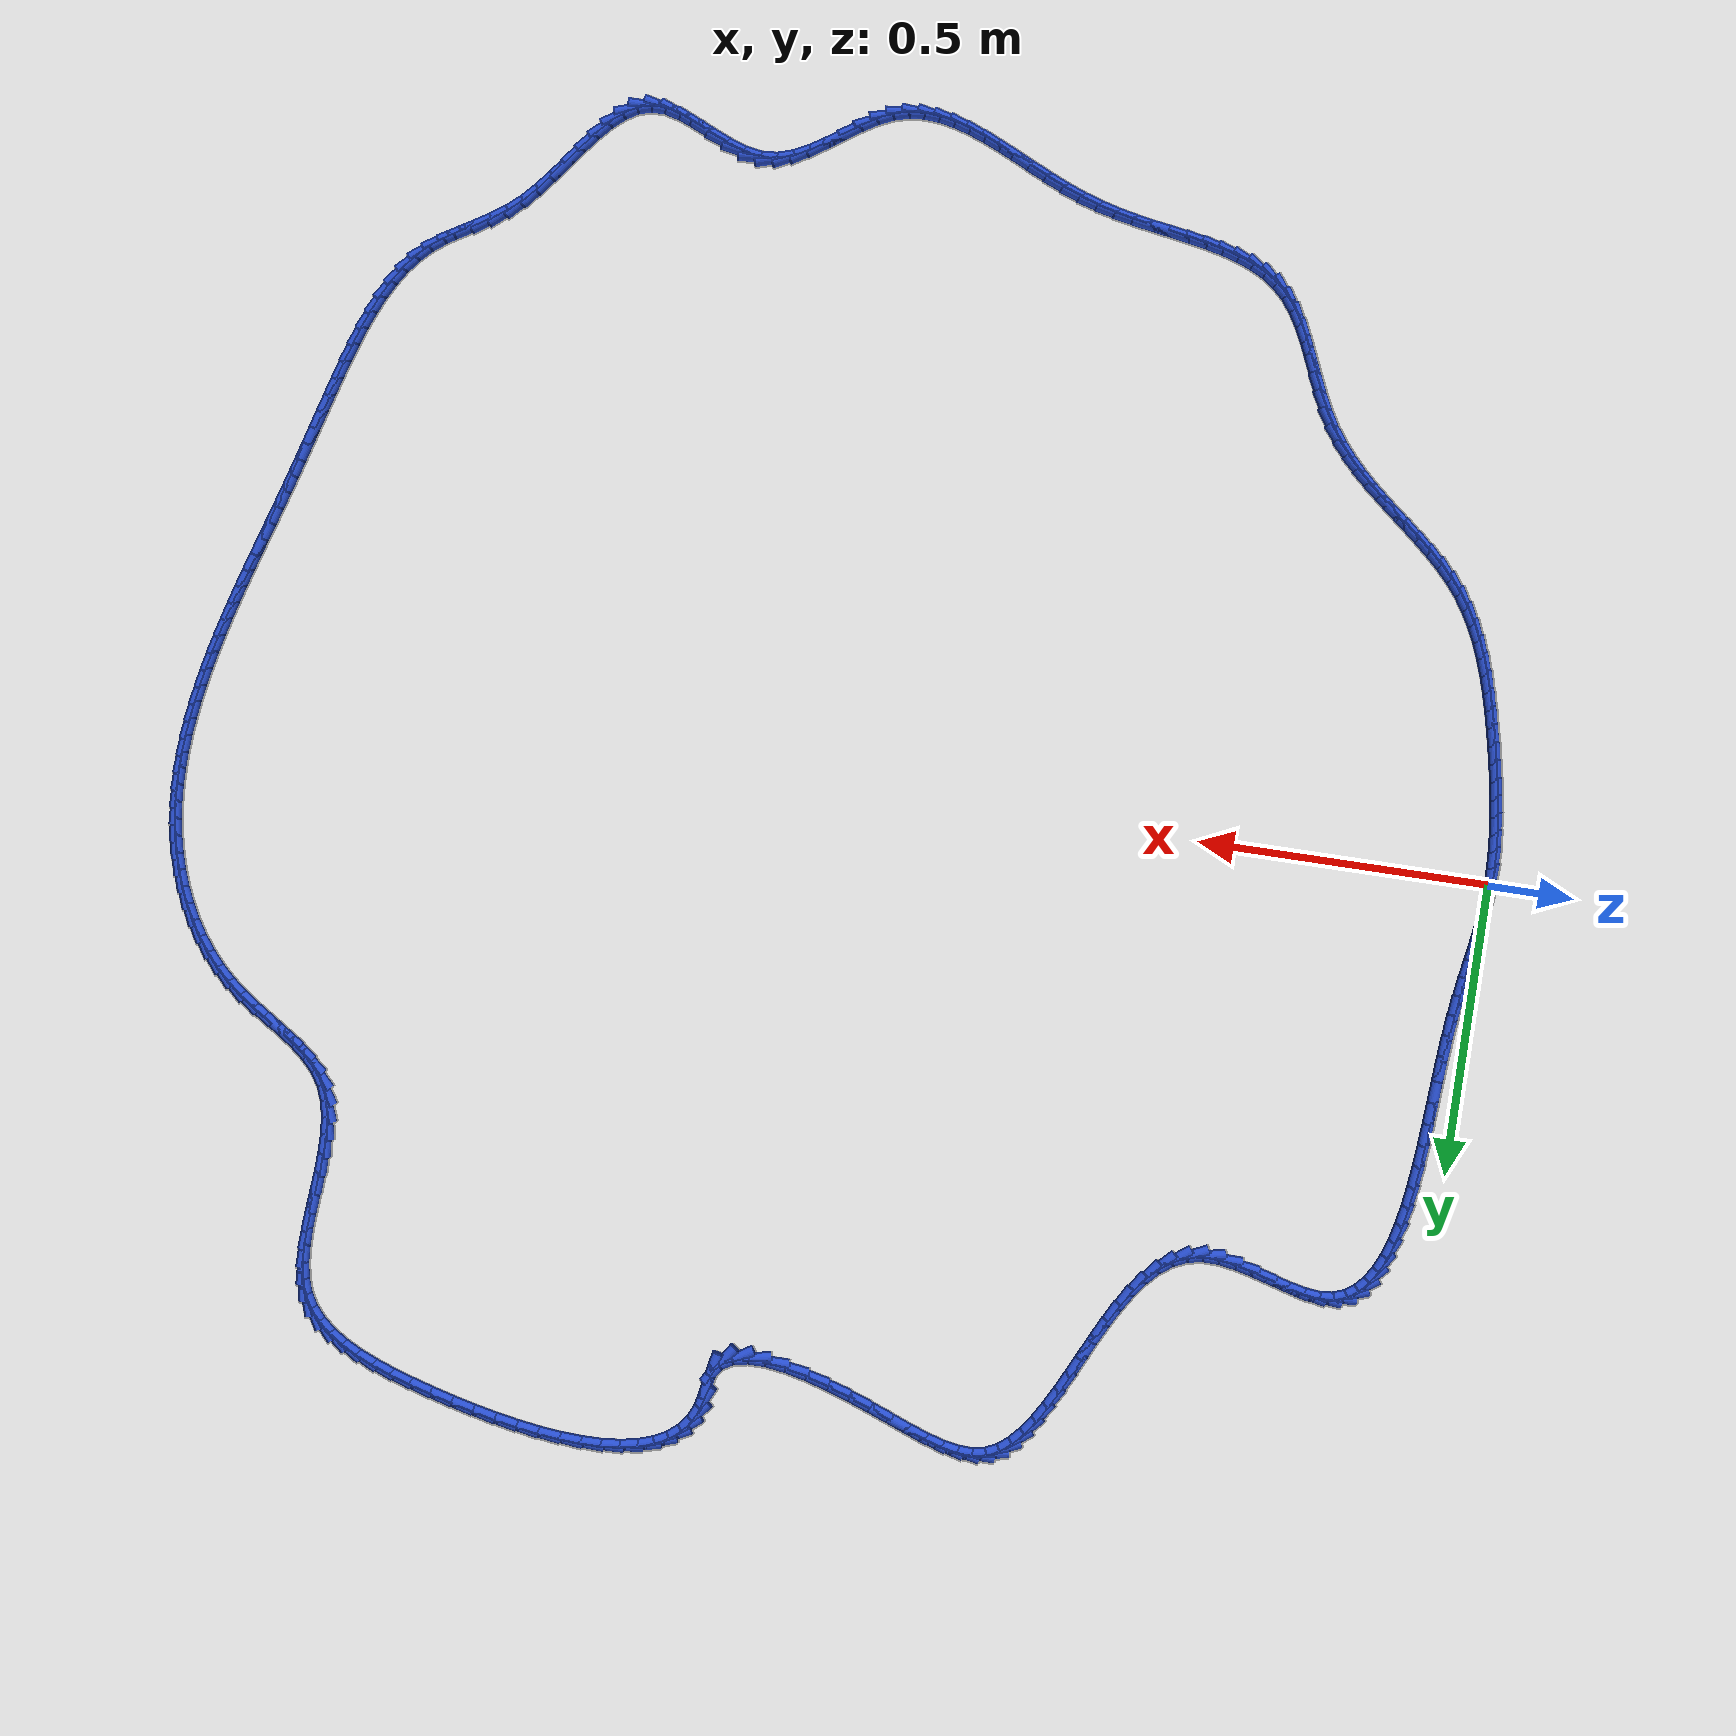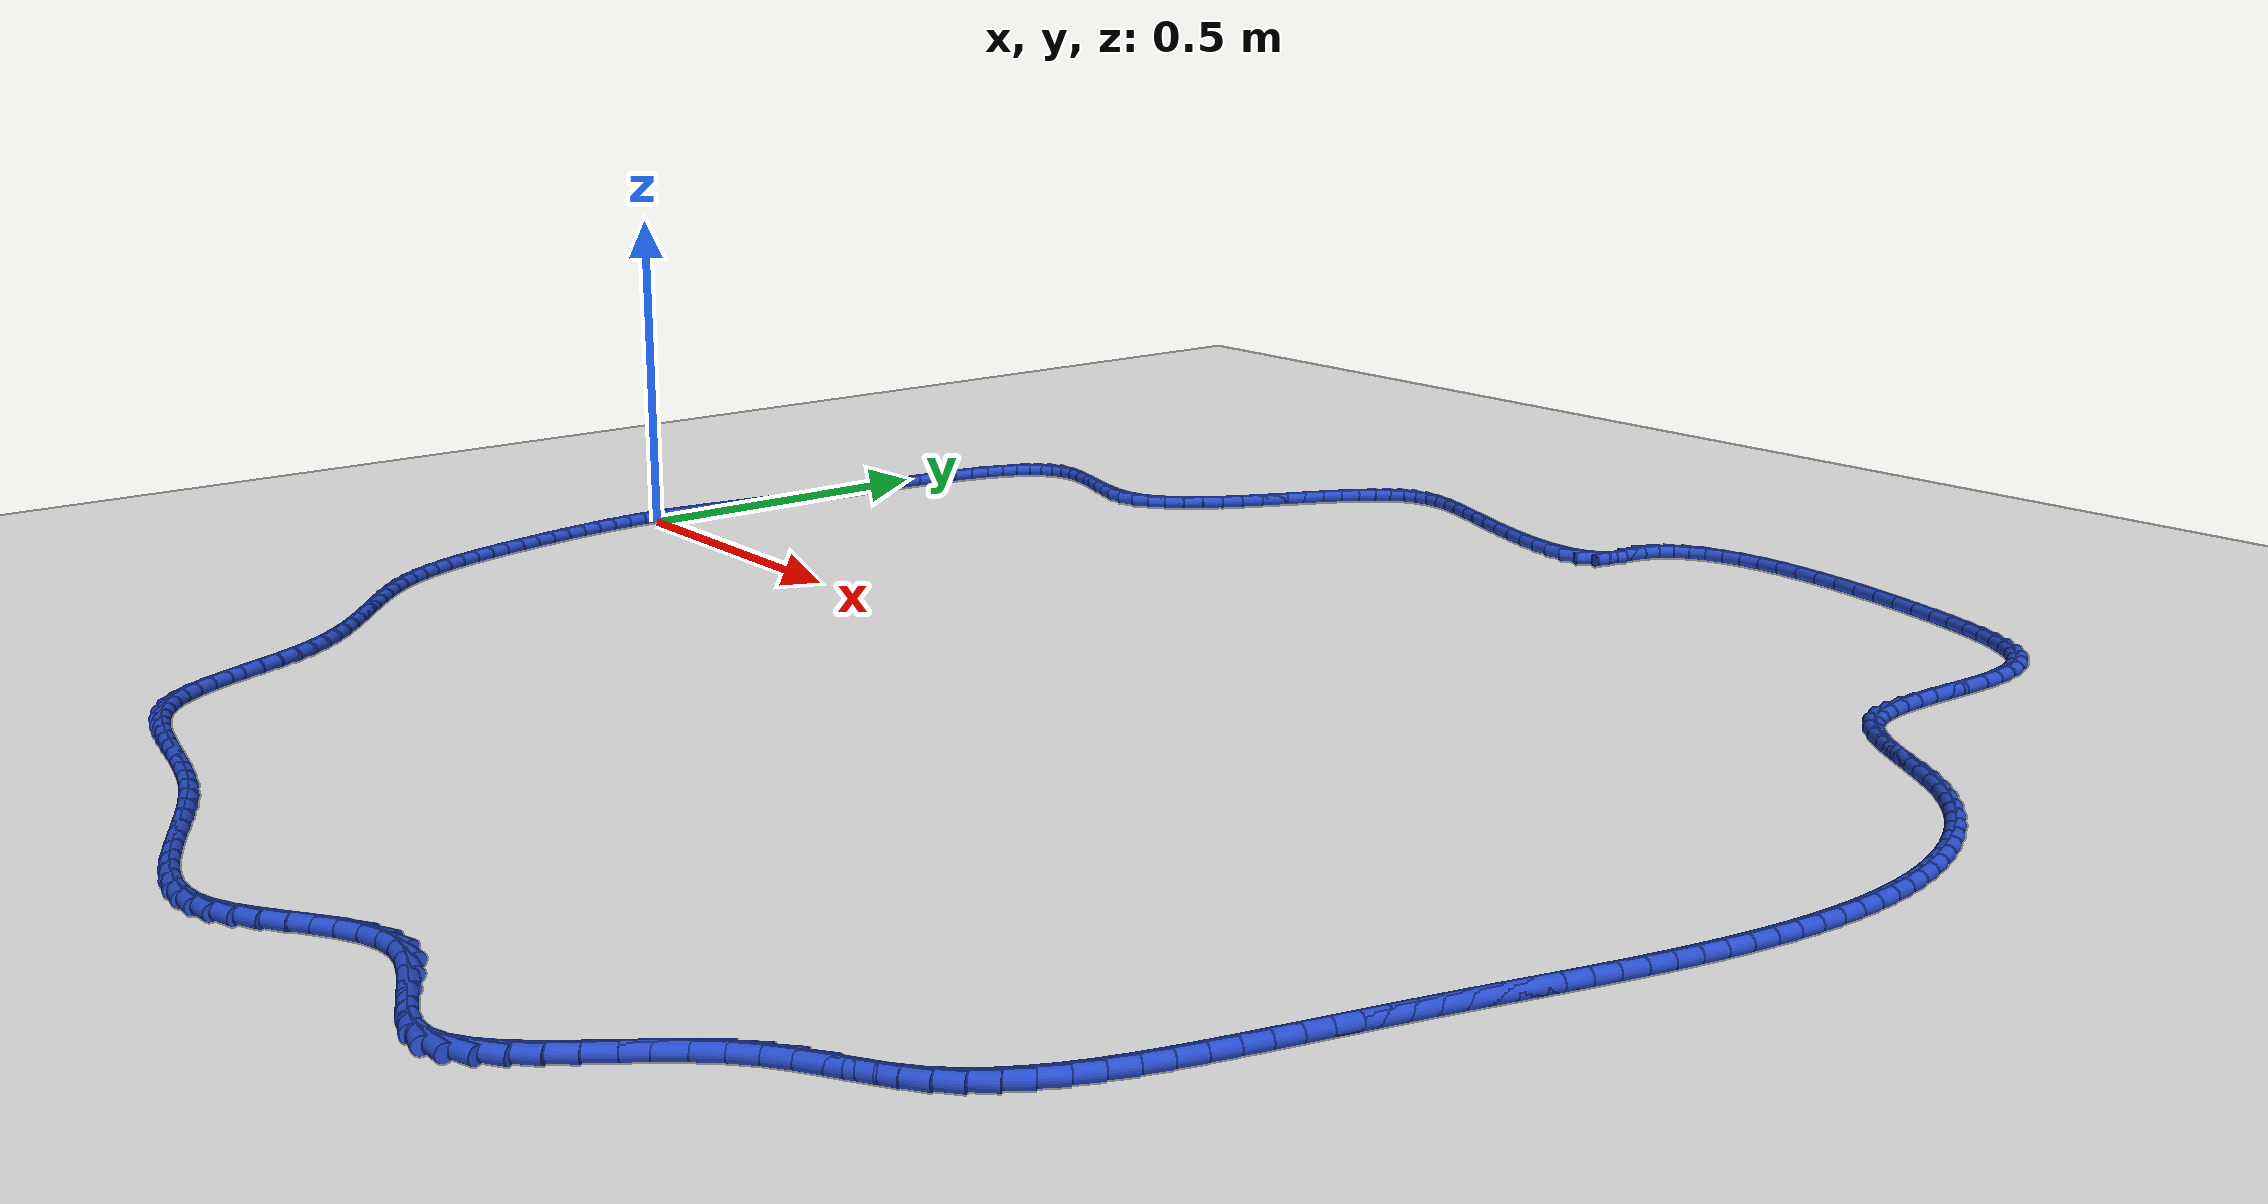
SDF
<sdf version="1.6">
 <world name="default">
  <light name="sun" type="directional">
   <pose>0 0 10 0 -0 0</pose>
   <diffuse>0.8 0.8 0.8 1</diffuse>
   <specular>0.2 0.2 0.2 1</specular>
   <attenuation>
    <range>1000</range>
    <constant>0.9</constant>
    <linear>0.01</linear>
    <quadratic>0.001</quadratic>
   </attenuation>
   <direction>-0.5 0.1 -0.9</direction>
  </light>
  <model name="ground_plane">
   <static>1</static>
   <link name="link">
    <collision name="collision">
     <geometry><plane><normal>0 0 1</normal><size>100 100</size></plane></geometry>
     <surface><friction><ode><mu>100</mu><mu2>50</mu2></ode></friction></surface>
    </collision>
    <visual name="visual">
     <cast_shadows>0</cast_shadows>
     <geometry><plane><normal>0 0 1</normal><size>100 100</size></plane></geometry>
     <material>
      <script><uri>file://media/materials/scripts/gazebo.material</uri><name>Gazebo/WhiteGlow</name></script>
     </material>
    </visual>
   </link>
  </model>
  <gravity>0 0 -9.8</gravity>
  <magnetic_field>6e-06 2.3e-05 -4.2e-05</magnetic_field>
  <atmosphere type="adiabatic"/>
  <physics name="default_physics" default="0" type="ode">
   <max_step_size>0.001</max_step_size>
   <real_time_factor>1</real_time_factor>
   <real_time_update_rate>1000</real_time_update_rate>
  </physics>
  <scene><ambient>0.4 0.4 0.4 1</ambient><background>0.7 0.7 0.7 1</background><shadows>1</shadows></scene>
  <spherical_coordinates>
   <surface_model>EARTH_WGS84</surface_model>
   <latitude_deg>0</latitude_deg>
   <longitude_deg>0</longitude_deg>
   <elevation>0</elevation>
   <heading_deg>0</heading_deg>
  </spherical_coordinates>
  <model name="line">
   <link name="link_0">
    <pose>-1.6479873021779667e-17 0.0 0.01 0 1.57 1.5184382656846507</pose>
    <collision name="collision">
     <geometry><cylinder><radius>0.01</radius><length>0.08</length></cylinder></geometry>
    </collision>
    <visual name="visual">
     <material>
      <script><name>Gazebo/Blue</name><uri>file://media/materials/scripts/gazebo.material</uri></script>
     </material>
     <geometry><cylinder><radius>0.01</radius><length>0.08</length></cylinder></geometry>
    </visual>
   </link>
   <link name="link_1">
    <pose>0.0014574475222923252 0.027810721952906785 0.01 0 1.57 1.4770112874705195</pose>
    <collision name="collision">
     <geometry><cylinder><radius>0.01</radius><length>0.08</length></cylinder></geometry>
    </collision>
    <visual name="visual">
     <material>
      <script><name>Gazebo/Blue</name><uri>file://media/materials/scripts/gazebo.material</uri></script>
     </material>
     <geometry><cylinder><radius>0.01</radius><length>0.08</length></cylinder></geometry>
    </visual>
   </link>
   <link name="link_2">
    <pose>0.004054440207986188 0.05542039371427029 0.01 0 1.57 1.4455119472380362</pose>
    <collision name="collision">
     <geometry><cylinder><radius>0.01</radius><length>0.08</length></cylinder></geometry>
    </collision>
    <visual name="visual">
     <material>
      <script><name>Gazebo/Blue</name><uri>file://media/materials/scripts/gazebo.material</uri></script>
     </material>
     <geometry><cylinder><radius>0.01</radius><length>0.08</length></cylinder></geometry>
    </visual>
   </link>
   <link name="link_3">
    <pose>0.007540841671047062 0.08310254612929184 0.01 0 1.57 1.424648393871587</pose>
    <collision name="collision">
     <geometry><cylinder><radius>0.01</radius><length>0.08</length></cylinder></geometry>
    </collision>
    <visual name="visual">
     <material>
      <script><name>Gazebo/Blue</name><uri>file://media/materials/scripts/gazebo.material</uri></script>
     </material>
     <geometry><cylinder><radius>0.01</radius><length>0.08</length></cylinder></geometry>
    </visual>
   </link>
   <link name="link_4">
    <pose>0.011666515525440456 0.11113071004317263 0.01 0 1.57 1.4144843685888346</pose>
    <collision name="collision">
     <geometry><cylinder><radius>0.01</radius><length>0.08</length></cylinder></geometry>
    </collision>
    <visual name="visual">
     <material>
      <script><name>Gazebo/Blue</name><uri>file://media/materials/scripts/gazebo.material</uri></script>
     </material>
     <geometry><cylinder><radius>0.01</radius><length>0.08</length></cylinder></geometry>
    </visual>
   </link>
   <link name="link_5">
    <pose>0.01618132538513185 0.13977841630111387 0.01 0 1.57 1.414542060446958</pose>
    <collision name="collision">
     <geometry><cylinder><radius>0.01</radius><length>0.08</length></cylinder></geometry>
    </collision>
    <visual name="visual">
     <material>
      <script><name>Gazebo/Blue</name><uri>file://media/materials/scripts/gazebo.material</uri></script>
     </material>
     <geometry><cylinder><radius>0.01</radius><length>0.08</length></cylinder></geometry>
    </visual>
   </link>
   <link name="link_6">
    <pose>0.020835134864086738 0.16931919574831683 0.01 0 1.57 1.423927315164349</pose>
    <collision name="collision">
     <geometry><cylinder><radius>0.01</radius><length>0.08</length></cylinder></geometry>
    </collision>
    <visual name="visual">
     <material>
      <script><name>Gazebo/Blue</name><uri>file://media/materials/scripts/gazebo.material</uri></script>
     </material>
     <geometry><cylinder><radius>0.01</radius><length>0.08</length></cylinder></geometry>
    </visual>
   </link>
   <link name="link_7">
    <pose>0.025377807576270624 0.20002657922998274 0.01 0 1.57 1.4414533479040172</pose>
    <collision name="collision">
     <geometry><cylinder><radius>0.01</radius><length>0.08</length></cylinder></geometry>
    </collision>
    <visual name="visual">
     <material>
      <script><name>Gazebo/Blue</name><uri>file://media/materials/scripts/gazebo.material</uri></script>
     </material>
     <geometry><cylinder><radius>0.01</radius><length>0.08</length></cylinder></geometry>
    </visual>
   </link>
   <link name="link_8">
    <pose>0.029559207135649 0.2321740975913128 0.01 0 1.57 1.4654073668593173</pose>
    <collision name="collision">
     <geometry><cylinder><radius>0.01</radius><length>0.08</length></cylinder></geometry>
    </collision>
    <visual name="visual">
     <material>
      <script><name>Gazebo/Blue</name><uri>file://media/materials/scripts/gazebo.material</uri></script>
     </material>
     <geometry><cylinder><radius>0.01</radius><length>0.08</length></cylinder></geometry>
    </visual>
   </link>
   <link name="link_9">
    <pose>0.03313945484801601 0.2660199844694474 0.01 0 1.57 1.4872548854704863</pose>
    <collision name="collision">
     <geometry><cylinder><radius>0.01</radius><length>0.08</length></cylinder></geometry>
    </collision>
    <visual name="visual">
     <material>
      <script><name>Gazebo/Blue</name><uri>file://media/materials/scripts/gazebo.material</uri></script>
     </material>
     <geometry><cylinder><radius>0.01</radius><length>0.08</length></cylinder></geometry>
    </visual>
   </link>
   <link name="link_10">
    <pose>0.03610869935225758 0.3014794357077643 0.01 0 1.57 1.500647299681323</pose>
    <collision name="collision">
     <geometry><cylinder><radius>0.01</radius><length>0.08</length></cylinder></geometry>
    </collision>
    <visual name="visual">
     <material>
      <script><name>Gazebo/Blue</name><uri>file://media/materials/scripts/gazebo.material</uri></script>
     </material>
     <geometry><cylinder><radius>0.01</radius><length>0.08</length></cylinder></geometry>
    </visual>
   </link>
   <link name="link_11">
    <pose>0.03868388604429441 0.3381294270863123 0.01 0 1.57 1.5065138532888493</pose>
    <collision name="collision">
     <geometry><cylinder><radius>0.01</radius><length>0.08</length></cylinder></geometry>
    </collision>
    <visual name="visual">
     <material>
      <script><name>Gazebo/Blue</name><uri>file://media/materials/scripts/gazebo.material</uri></script>
     </material>
     <geometry><cylinder><radius>0.01</radius><length>0.08</length></cylinder></geometry>
    </visual>
   </link>
   <link name="link_12">
    <pose>0.041091571856145315 0.3755326007835918 0.01 0 1.57 1.5054914585599306</pose>
    <collision name="collision">
     <geometry><cylinder><radius>0.01</radius><length>0.08</length></cylinder></geometry>
    </collision>
    <visual name="visual">
     <material>
      <script><name>Gazebo/Blue</name><uri>file://media/materials/scripts/gazebo.material</uri></script>
     </material>
     <geometry><cylinder><radius>0.01</radius><length>0.08</length></cylinder></geometry>
    </visual>
   </link>
   <link name="link_13">
    <pose>0.043558313719829087 0.4132515989781033 0.01 0 1.57 1.497720817772451</pose>
    <collision name="collision">
     <geometry><cylinder><radius>0.01</radius><length>0.08</length></cylinder></geometry>
    </collision>
    <visual name="visual">
     <material>
      <script><name>Gazebo/Blue</name><uri>file://media/materials/scripts/gazebo.material</uri></script>
     </material>
     <geometry><cylinder><radius>0.01</radius><length>0.08</length></cylinder></geometry>
    </visual>
   </link>
   <link name="link_14">
    <pose>0.04631066856736449 0.4508490638483472 0.01 0 1.57 1.4828849888272446</pose>
    <collision name="collision">
     <geometry><cylinder><radius>0.01</radius><length>0.08</length></cylinder></geometry>
    </collision>
    <visual name="visual">
     <material>
      <script><name>Gazebo/Blue</name><uri>file://media/materials/scripts/gazebo.material</uri></script>
     </material>
     <geometry><cylinder><radius>0.01</radius><length>0.08</length></cylinder></geometry>
    </visual>
   </link>
   <link name="link_15">
    <pose>0.049575193330770304 0.487887637572824 0.01 0 1.57 1.460178876890645</pose>
    <collision name="collision">
     <geometry><cylinder><radius>0.01</radius><length>0.08</length></cylinder></geometry>
    </collision>
    <visual name="visual">
     <material>
      <script><name>Gazebo/Blue</name><uri>file://media/materials/scripts/gazebo.material</uri></script>
     </material>
     <geometry><cylinder><radius>0.01</radius><length>0.08</length></cylinder></geometry>
    </visual>
   </link>
   <link name="link_16">
    <pose>0.053578444942065345 0.5239299623300342 0.01 0 1.57 1.428207487026027</pose>
    <collision name="collision">
     <geometry><cylinder><radius>0.01</radius><length>0.08</length></cylinder></geometry>
    </collision>
    <visual name="visual">
     <material>
      <script><name>Gazebo/Blue</name><uri>file://media/materials/scripts/gazebo.material</uri></script>
     </material>
     <geometry><cylinder><radius>0.01</radius><length>0.08</length></cylinder></geometry>
    </visual>
   </link>
   <link name="link_17">
    <pose>0.0585469803332684 0.5585386802984782 0.01 0 1.57 1.3847978749277365</pose>
    <collision name="collision">
     <geometry><cylinder><radius>0.01</radius><length>0.08</length></cylinder></geometry>
    </collision>
    <visual name="visual">
     <material>
      <script><name>Gazebo/Blue</name><uri>file://media/materials/scripts/gazebo.material</uri></script>
     </material>
     <geometry><cylinder><radius>0.01</radius><length>0.08</length></cylinder></geometry>
    </visual>
   </link>
   <link name="link_18">
    <pose>0.06470735643639822 0.5912764336566566 0.01 0 1.57 1.326701956054612</pose>
    <collision name="collision">
     <geometry><cylinder><radius>0.01</radius><length>0.08</length></cylinder></geometry>
    </collision>
    <visual name="visual">
     <material>
      <script><name>Gazebo/Blue</name><uri>file://media/materials/scripts/gazebo.material</uri></script>
     </material>
     <geometry><cylinder><radius>0.01</radius><length>0.08</length></cylinder></geometry>
    </visual>
   </link>
   <link name="link_19">
    <pose>0.0722861301834736 0.6217058645830695 0.01 0 1.57 1.2491819491159826</pose>
    <collision name="collision">
     <geometry><cylinder><radius>0.01</radius><length>0.08</length></cylinder></geometry>
    </collision>
    <visual name="visual">
     <material>
      <script><name>Gazebo/Blue</name><uri>file://media/materials/scripts/gazebo.material</uri></script>
     </material>
     <geometry><cylinder><radius>0.01</radius><length>0.08</length></cylinder></geometry>
    </visual>
   </link>
   <link name="link_20">
    <pose>0.08150985850651336 0.649389615256218 0.01 0 1.57 1.1455717473456568</pose>
    <collision name="collision">
     <geometry><cylinder><radius>0.01</radius><length>0.08</length></cylinder></geometry>
    </collision>
    <visual name="visual">
     <material>
      <script><name>Gazebo/Blue</name><uri>file://media/materials/scripts/gazebo.material</uri></script>
     </material>
     <geometry><cylinder><radius>0.01</radius><length>0.08</length></cylinder></geometry>
    </visual>
   </link>
   <link name="link_21">
    <pose>0.09260509833753626 0.6738903278546018 0.01 0 1.57 1.0072835828882964</pose>
    <collision name="collision">
     <geometry><cylinder><radius>0.01</radius><length>0.08</length></cylinder></geometry>
    </collision>
    <visual name="visual">
     <material>
      <script><name>Gazebo/Blue</name><uri>file://media/materials/scripts/gazebo.material</uri></script>
     </material>
     <geometry><cylinder><radius>0.01</radius><length>0.08</length></cylinder></geometry>
    </visual>
   </link>
   <link name="link_22">
    <pose>0.10579840660856102 0.6947706445567218 0.01 0 1.57 0.8257167259240422</pose>
    <collision name="collision">
     <geometry><cylinder><radius>0.01</radius><length>0.08</length></cylinder></geometry>
    </collision>
    <visual name="visual">
     <material>
      <script><name>Gazebo/Blue</name><uri>file://media/materials/scripts/gazebo.material</uri></script>
     </material>
     <geometry><cylinder><radius>0.01</radius><length>0.08</length></cylinder></geometry>
    </visual>
   </link>
   <link name="link_23">
    <pose>0.12131634025160658 0.7115932075410786 0.01 0 1.57 0.5987059527208497</pose>
    <collision name="collision">
     <geometry><cylinder><radius>0.01</radius><length>0.08</length></cylinder></geometry>
    </collision>
    <visual name="visual">
     <material>
      <script><name>Gazebo/Blue</name><uri>file://media/materials/scripts/gazebo.material</uri></script>
     </material>
     <geometry><cylinder><radius>0.01</radius><length>0.08</length></cylinder></geometry>
    </visual>
   </link>
   <link name="link_24">
    <pose>0.13938545619869164 0.7239206589861725 0.01 0 1.57 0.34088142372437685</pose>
    <collision name="collision">
     <geometry><cylinder><radius>0.01</radius><length>0.08</length></cylinder></geometry>
    </collision>
    <visual name="visual">
     <material>
      <script><name>Gazebo/Blue</name><uri>file://media/materials/scripts/gazebo.material</uri></script>
     </material>
     <geometry><cylinder><radius>0.01</radius><length>0.08</length></cylinder></geometry>
    </visual>
   </link>
   <link name="link_25">
    <pose>0.1602323113818349 0.7313156410705037 0.01 0 1.57 0.08552155814563012</pose>
    <collision name="collision">
     <geometry><cylinder><radius>0.01</radius><length>0.08</length></cylinder></geometry>
    </collision>
    <visual name="visual">
     <material>
      <script><name>Gazebo/Blue</name><uri>file://media/materials/scripts/gazebo.material</uri></script>
     </material>
     <geometry><cylinder><radius>0.01</radius><length>0.08</length></cylinder></geometry>
    </visual>
   </link>
   <link name="link_26">
    <pose>0.1840744512960569 0.7333596436923977 0.01 0 1.57 -0.10899472382913782</pose>
    <collision name="collision">
     <geometry><cylinder><radius>0.01</radius><length>0.08</length></cylinder></geometry>
    </collision>
    <visual name="visual">
     <material>
      <script><name>Gazebo/Blue</name><uri>file://media/materials/scripts/gazebo.material</uri></script>
     </material>
     <geometry><cylinder><radius>0.01</radius><length>0.08</length></cylinder></geometry>
    </visual>
   </link>
   <link name="link_27">
    <pose>0.21074351606767266 0.7304412906478425 0.01 0 1.57 -0.21858061651169342</pose>
    <collision name="collision">
     <geometry><cylinder><radius>0.01</radius><length>0.08</length></cylinder></geometry>
    </collision>
    <visual name="visual">
     <material>
      <script><name>Gazebo/Blue</name><uri>file://media/materials/scripts/gazebo.material</uri></script>
     </material>
     <geometry><cylinder><radius>0.01</radius><length>0.08</length></cylinder></geometry>
    </visual>
   </link>
   <link name="link_28">
    <pose>0.23954822387258012 0.7240429143625616 0.01 0 1.57 -0.2686732767853013</pose>
    <collision name="collision">
     <geometry><cylinder><radius>0.01</radius><length>0.08</length></cylinder></geometry>
    </collision>
    <visual name="visual">
     <material>
      <script><name>Gazebo/Blue</name><uri>file://media/materials/scripts/gazebo.material</uri></script>
     </material>
     <geometry><cylinder><radius>0.01</radius><length>0.08</length></cylinder></geometry>
    </visual>
   </link>
   <link name="link_29">
    <pose>0.26976008262744194 0.7157246737555208 0.01 0 1.57 -0.2738670696774084</pose>
    <collision name="collision">
     <geometry><cylinder><radius>0.01</radius><length>0.08</length></cylinder></geometry>
    </collision>
    <visual name="visual">
     <material>
      <script><name>Gazebo/Blue</name><uri>file://media/materials/scripts/gazebo.material</uri></script>
     </material>
     <geometry><cylinder><radius>0.01</radius><length>0.08</length></cylinder></geometry>
    </visual>
   </link>
   <link name="link_30">
    <pose>0.3006506002489206 0.7070467277456862 0.01 0 1.57 -0.23786541721052984</pose>
    <collision name="collision">
     <geometry><cylinder><radius>0.01</radius><length>0.08</length></cylinder></geometry>
    </collision>
    <visual name="visual">
     <material>
      <script><name>Gazebo/Blue</name><uri>file://media/materials/scripts/gazebo.material</uri></script>
     </material>
     <geometry><cylinder><radius>0.01</radius><length>0.08</length></cylinder></geometry>
    </visual>
   </link>
   <link name="link_31">
    <pose>0.33149128465367916 0.6995692352520233 0.01 0 1.57 -0.15563430187163324</pose>
    <collision name="collision">
     <geometry><cylinder><radius>0.01</radius><length>0.08</length></cylinder></geometry>
    </collision>
    <visual name="visual">
     <material>
      <script><name>Gazebo/Blue</name><uri>file://media/materials/scripts/gazebo.material</uri></script>
     </material>
     <geometry><cylinder><radius>0.01</radius><length>0.08</length></cylinder></geometry>
    </visual>
   </link>
   <link name="link_32">
    <pose>0.36155364375838006 0.6948523551934981 0.01 0 1.57 -0.013870628158267779</pose>
    <collision name="collision">
     <geometry><cylinder><radius>0.01</radius><length>0.08</length></cylinder></geometry>
    </collision>
    <visual name="visual">
     <material>
      <script><name>Gazebo/Blue</name><uri>file://media/materials/scripts/gazebo.material</uri></script>
     </material>
     <geometry><cylinder><radius>0.01</radius><length>0.08</length></cylinder></geometry>
    </visual>
   </link>
   <link name="link_33">
    <pose>0.3901091854796858 0.6944562464890758 0.01 0 1.57 0.20102334938266286</pose>
    <collision name="collision">
     <geometry><cylinder><radius>0.01</radius><length>0.08</length></cylinder></geometry>
    </collision>
    <visual name="visual">
     <material>
      <script><name>Gazebo/Blue</name><uri>file://media/materials/scripts/gazebo.material</uri></script>
     </material>
     <geometry><cylinder><radius>0.01</radius><length>0.08</length></cylinder></geometry>
    </visual>
   </link>
   <link name="link_34">
    <pose>0.41647738447328136 0.6998294435664786 0.01 0 1.57 0.4379355023624844</pose>
    <collision name="collision">
     <geometry><cylinder><radius>0.01</radius><length>0.08</length></cylinder></geometry>
    </collision>
    <visual name="visual">
     <material>
      <script><name>Gazebo/Blue</name><uri>file://media/materials/scripts/gazebo.material</uri></script>
     </material>
     <geometry><cylinder><radius>0.01</radius><length>0.08</length></cylinder></geometry>
    </visual>
   </link>
   <link name="link_35">
    <pose>0.4405453479932527 0.7110995301008451 0.01 0 1.57 0.6409313779787396</pose>
    <collision name="collision">
     <geometry><cylinder><radius>0.01</radius><length>0.08</length></cylinder></geometry>
    </collision>
    <visual name="visual">
     <material>
      <script><name>Gazebo/Blue</name><uri>file://media/materials/scripts/gazebo.material</uri></script>
     </material>
     <geometry><cylinder><radius>0.01</radius><length>0.08</length></cylinder></geometry>
    </visual>
   </link>
   <link name="link_36">
    <pose>0.4625712122363233 0.7275306598614439 0.01 0 1.57 0.7998318997861417</pose>
    <collision name="collision">
     <geometry><cylinder><radius>0.01</radius><length>0.08</length></cylinder></geometry>
    </collision>
    <visual name="visual">
     <material>
      <script><name>Gazebo/Blue</name><uri>file://media/materials/scripts/gazebo.material</uri></script>
     </material>
     <geometry><cylinder><radius>0.01</radius><length>0.08</length></cylinder></geometry>
    </visual>
   </link>
   <link name="link_37">
    <pose>0.4828195171551275 0.7483720842912598 0.01 0 1.57 0.9179690309820943</pose>
    <collision name="collision">
     <geometry><cylinder><radius>0.01</radius><length>0.08</length></cylinder></geometry>
    </collision>
    <visual name="visual">
     <material>
      <script><name>Gazebo/Blue</name><uri>file://media/materials/scripts/gazebo.material</uri></script>
     </material>
     <geometry><cylinder><radius>0.01</radius><length>0.08</length></cylinder></geometry>
    </visual>
   </link>
   <link name="link_38">
    <pose>0.5015548027023005 0.772873054833278 0.01 0 1.57 1.0029194961640735</pose>
    <collision name="collision">
     <geometry><cylinder><radius>0.01</radius><length>0.08</length></cylinder></geometry>
    </collision>
    <visual name="visual">
     <material>
      <script><name>Gazebo/Blue</name><uri>file://media/materials/scripts/gazebo.material</uri></script>
     </material>
     <geometry><cylinder><radius>0.01</radius><length>0.08</length></cylinder></geometry>
    </visual>
   </link>
   <link name="link_39">
    <pose>0.5190416088304769 0.8002828229304835 0.01 0 1.57 1.061728043392184</pose>
    <collision name="collision">
     <geometry><cylinder><radius>0.01</radius><length>0.08</length></cylinder></geometry>
    </collision>
    <visual name="visual">
     <material>
      <script><name>Gazebo/Blue</name><uri>file://media/materials/scripts/gazebo.material</uri></script>
     </material>
     <geometry><cylinder><radius>0.01</radius><length>0.08</length></cylinder></geometry>
    </visual>
   </link>
   <link name="link_40">
    <pose>0.5355444754922911 0.8298506400258613 0.01 0 1.57 1.0995354778672064</pose>
    <collision name="collision">
     <geometry><cylinder><radius>0.01</radius><length>0.08</length></cylinder></geometry>
    </collision>
    <visual name="visual">
     <material>
      <script><name>Gazebo/Blue</name><uri>file://media/materials/scripts/gazebo.material</uri></script>
     </material>
     <geometry><cylinder><radius>0.01</radius><length>0.08</length></cylinder></geometry>
    </visual>
   </link>
   <link name="link_41">
    <pose>0.551327942640378 0.8608257575623959 0.01 0 1.57 1.1195469896317325</pose>
    <collision name="collision">
     <geometry><cylinder><radius>0.01</radius><length>0.08</length></cylinder></geometry>
    </collision>
    <visual name="visual">
     <material>
      <script><name>Gazebo/Blue</name><uri>file://media/materials/scripts/gazebo.material</uri></script>
     </material>
     <geometry><cylinder><radius>0.01</radius><length>0.08</length></cylinder></geometry>
    </visual>
   </link>
   <link name="link_42">
    <pose>0.5666565502273726 0.892457426983073 0.01 0 1.57 1.1232685931399682</pose>
    <collision name="collision">
     <geometry><cylinder><radius>0.01</radius><length>0.08</length></cylinder></geometry>
    </collision>
    <visual name="visual">
     <material>
      <script><name>Gazebo/Blue</name><uri>file://media/materials/scripts/gazebo.material</uri></script>
     </material>
     <geometry><cylinder><radius>0.01</radius><length>0.08</length></cylinder></geometry>
    </visual>
   </link>
   <link name="link_43">
    <pose>0.5817948382059095 0.9239948997308772 0.01 0 1.57 1.1106411237291867</pose>
    <collision name="collision">
     <geometry><cylinder><radius>0.01</radius><length>0.08</length></cylinder></geometry>
    </collision>
    <visual name="visual">
     <material>
      <script><name>Gazebo/Blue</name><uri>file://media/materials/scripts/gazebo.material</uri></script>
     </material>
     <geometry><cylinder><radius>0.01</radius><length>0.08</length></cylinder></geometry>
    </visual>
   </link>
   <link name="link_44">
    <pose>0.5970073465286229 0.9546874272487932 0.01 0 1.57 1.0799575738453326</pose>
    <collision name="collision">
     <geometry><cylinder><radius>0.01</radius><length>0.08</length></cylinder></geometry>
    </collision>
    <visual name="visual">
     <material>
      <script><name>Gazebo/Blue</name><uri>file://media/materials/scripts/gazebo.material</uri></script>
     </material>
     <geometry><cylinder><radius>0.01</radius><length>0.08</length></cylinder></geometry>
    </visual>
   </link>
   <link name="link_45">
    <pose>0.612558615148148 0.9837842609798066 0.01 0 1.57 1.0275139071233523</pose>
    <collision name="collision">
     <geometry><cylinder><radius>0.01</radius><length>0.08</length></cylinder></geometry>
    </collision>
    <visual name="visual">
     <material>
      <script><name>Gazebo/Blue</name><uri>file://media/materials/scripts/gazebo.material</uri></script>
     </material>
     <geometry><cylinder><radius>0.01</radius><length>0.08</length></cylinder></geometry>
    </visual>
   </link>
   <link name="link_46">
    <pose>0.6287131840171197 1.0105346523669023 0.01 0 1.57 0.9469931408486344</pose>
    <collision name="collision">
     <geometry><cylinder><radius>0.01</radius><length>0.08</length></cylinder></geometry>
    </collision>
    <visual name="visual">
     <material>
      <script><name>Gazebo/Blue</name><uri>file://media/materials/scripts/gazebo.material</uri></script>
     </material>
     <geometry><cylinder><radius>0.01</radius><length>0.08</length></cylinder></geometry>
    </visual>
   </link>
   <link name="link_47">
    <pose>0.6457355930881725 1.0341878528530652 0.01 0 1.57 0.828849974729655</pose>
    <collision name="collision">
     <geometry><cylinder><radius>0.01</radius><length>0.08</length></cylinder></geometry>
    </collision>
    <visual name="visual">
     <material>
      <script><name>Gazebo/Blue</name><uri>file://media/materials/scripts/gazebo.material</uri></script>
     </material>
     <geometry><cylinder><radius>0.01</radius><length>0.08</length></cylinder></geometry>
    </visual>
   </link>
   <link name="link_48">
    <pose>0.663890382313941 1.05399311388128 0.01 0 1.57 0.6610332251564337</pose>
    <collision name="collision">
     <geometry><cylinder><radius>0.01</radius><length>0.08</length></cylinder></geometry>
    </collision>
    <visual name="visual">
     <material>
      <script><name>Gazebo/Blue</name><uri>file://media/materials/scripts/gazebo.material</uri></script>
     </material>
     <geometry><cylinder><radius>0.01</radius><length>0.08</length></cylinder></geometry>
    </visual>
   </link>
   <link name="link_49">
    <pose>0.6834420916470603 1.069199686894532 0.01 0 1.57 0.43502017714248226</pose>
    <collision name="collision">
     <geometry><cylinder><radius>0.01</radius><length>0.08</length></cylinder></geometry>
    </collision>
    <visual name="visual">
     <material>
      <script><name>Gazebo/Blue</name><uri>file://media/materials/scripts/gazebo.material</uri></script>
     </material>
     <geometry><cylinder><radius>0.01</radius><length>0.08</length></cylinder></geometry>
    </visual>
   </link>
   <link name="link_50">
    <pose>0.7046551588923999 1.0790576364832445 0.01 0 1.57 0.1778824332695893</pose>
    <collision name="collision">
     <geometry><cylinder><radius>0.01</radius><length>0.08</length></cylinder></geometry>
    </collision>
    <visual name="visual">
     <material>
      <script><name>Gazebo/Blue</name><uri>file://media/materials/scripts/gazebo.material</uri></script>
     </material>
     <geometry><cylinder><radius>0.01</radius><length>0.08</length></cylinder></geometry>
    </visual>
   </link>
   <link name="link_51">
    <pose>0.7277448127488982 1.0832087564010004 0.01 0 1.57 -0.03568982639180302</pose>
    <collision name="collision">
     <geometry><cylinder><radius>0.01</radius><length>0.08</length></cylinder></geometry>
    </collision>
    <visual name="visual">
     <material>
      <script><name>Gazebo/Blue</name><uri>file://media/materials/scripts/gazebo.material</uri></script>
     </material>
     <geometry><cylinder><radius>0.01</radius><length>0.08</length></cylinder></geometry>
    </visual>
   </link>
   <link name="link_52">
    <pose>0.7527982266461936 1.0823142245688333 0.01 0 1.57 -0.18667077159956472</pose>
    <collision name="collision">
     <geometry><cylinder><radius>0.01</radius><length>0.08</length></cylinder></geometry>
    </collision>
    <visual name="visual">
     <material>
      <script><name>Gazebo/Blue</name><uri>file://media/materials/scripts/gazebo.material</uri></script>
     </material>
     <geometry><cylinder><radius>0.01</radius><length>0.08</length></cylinder></geometry>
    </visual>
   </link>
   <link name="link_53">
    <pose>0.7798820099178788 1.0771989194258498 0.01 0 1.57 -0.28379867088600436</pose>
    <collision name="collision">
     <geometry><cylinder><radius>0.01</radius><length>0.08</length></cylinder></geometry>
    </collision>
    <visual name="visual">
     <material>
      <script><name>Gazebo/Blue</name><uri>file://media/materials/scripts/gazebo.material</uri></script>
     </material>
     <geometry><cylinder><radius>0.01</radius><length>0.08</length></cylinder></geometry>
    </visual>
   </link>
   <link name="link_54">
    <pose>0.8090627718975479 1.068687719411155 0.01 0 1.57 -0.33984584873237744</pose>
    <collision name="collision">
     <geometry><cylinder><radius>0.01</radius><length>0.08</length></cylinder></geometry>
    </collision>
    <visual name="visual">
     <material>
      <script><name>Gazebo/Blue</name><uri>file://media/materials/scripts/gazebo.material</uri></script>
     </material>
     <geometry><cylinder><radius>0.01</radius><length>0.08</length></cylinder></geometry>
    </visual>
   </link>
   <link name="link_55">
    <pose>0.8404071219187935 1.0576055029638551 0.01 0 1.57 -0.3649682735976568</pose>
    <collision name="collision">
     <geometry><cylinder><radius>0.01</radius><length>0.08</length></cylinder></geometry>
    </collision>
    <visual name="visual">
     <material>
      <script><name>Gazebo/Blue</name><uri>file://media/materials/scripts/gazebo.material</uri></script>
     </material>
     <geometry><cylinder><radius>0.01</radius><length>0.08</length></cylinder></geometry>
    </visual>
   </link>
   <link name="link_56">
    <pose>0.8739816693152087 1.044777148523056 0.01 0 1.57 -0.36606762458616404</pose>
    <collision name="collision">
     <geometry><cylinder><radius>0.01</radius><length>0.08</length></cylinder></geometry>
    </collision>
    <visual name="visual">
     <material>
      <script><name>Gazebo/Blue</name><uri>file://media/materials/scripts/gazebo.material</uri></script>
     </material>
     <geometry><cylinder><radius>0.01</radius><length>0.08</length></cylinder></geometry>
    </visual>
   </link>
   <link name="link_57">
    <pose>0.9098477865228428 1.0310280132841756 0.01 0 1.57 -0.35017786426880093</pose>
    <collision name="collision">
     <geometry><cylinder><radius>0.01</radius><length>0.08</length></cylinder></geometry>
    </collision>
    <visual name="visual">
     <material>
      <script><name>Gazebo/Blue</name><uri>file://media/materials/scripts/gazebo.material</uri></script>
     </material>
     <geometry><cylinder><radius>0.01</radius><length>0.08</length></cylinder></geometry>
    </visual>
   </link>
   <link name="link_58">
    <pose>0.9476498017102475 1.0172215805609783 0.01 0 1.57 -0.32280895303635965</pose>
    <collision name="collision">
     <geometry><cylinder><radius>0.01</radius><length>0.08</length></cylinder></geometry>
    </collision>
    <visual name="visual">
     <material>
      <script><name>Gazebo/Blue</name><uri>file://media/materials/scripts/gazebo.material</uri></script>
     </material>
     <geometry><cylinder><radius>0.01</radius><length>0.08</length></cylinder></geometry>
    </visual>
   </link>
   <link name="link_59">
    <pose>0.9863183289214588 1.0042865812951123 0.01 0 1.57 -0.2821059428821999</pose>
    <collision name="collision">
     <geometry><cylinder><radius>0.01</radius><length>0.08</length></cylinder></geometry>
    </collision>
    <visual name="visual">
     <material>
      <script><name>Gazebo/Blue</name><uri>file://media/materials/scripts/gazebo.material</uri></script>
     </material>
     <geometry><cylinder><radius>0.01</radius><length>0.08</length></cylinder></geometry>
    </visual>
   </link>
   <link name="link_60">
    <pose>1.024713987375562 0.9931581453436117 0.01 0 1.57 -0.2229989032277991</pose>
    <collision name="collision">
     <geometry><cylinder><radius>0.01</radius><length>0.08</length></cylinder></geometry>
    </collision>
    <visual name="visual">
     <material>
      <script><name>Gazebo/Blue</name><uri>file://media/materials/scripts/gazebo.material</uri></script>
     </material>
     <geometry><cylinder><radius>0.01</radius><length>0.08</length></cylinder></geometry>
    </visual>
   </link>
   <link name="link_61">
    <pose>1.0616973962916436 0.9847714025635098 0.01 0 1.57 -0.13594617774612047</pose>
    <collision name="collision">
     <geometry><cylinder><radius>0.01</radius><length>0.08</length></cylinder></geometry>
    </collision>
    <visual name="visual">
     <material>
      <script><name>Gazebo/Blue</name><uri>file://media/materials/scripts/gazebo.material</uri></script>
     </material>
     <geometry><cylinder><radius>0.01</radius><length>0.08</length></cylinder></geometry>
    </visual>
   </link>
   <link name="link_62">
    <pose>1.096129174888789 0.9800614828118406 0.01 0 1.57 -0.003186860398285416</pose>
    <collision name="collision">
     <geometry><cylinder><radius>0.01</radius><length>0.08</length></cylinder></geometry>
    </collision>
    <visual name="visual">
     <material>
      <script><name>Gazebo/Blue</name><uri>file://media/materials/scripts/gazebo.material</uri></script>
     </material>
     <geometry><cylinder><radius>0.01</radius><length>0.08</length></cylinder></geometry>
    </visual>
   </link>
   <link name="link_63">
    <pose>1.1268699423860835 0.9799635159456372 0.01 0 1.57 0.20728556282290742</pose>
    <collision name="collision">
     <geometry><cylinder><radius>0.01</radius><length>0.08</length></cylinder></geometry>
    </collision>
    <visual name="visual">
     <material>
      <script><name>Gazebo/Blue</name><uri>file://media/materials/scripts/gazebo.material</uri></script>
     </material>
     <geometry><cylinder><radius>0.01</radius><length>0.08</length></cylinder></geometry>
    </visual>
   </link>
   <link name="link_64">
    <pose>1.152780318002614 0.9854126318219341 0.01 0 1.57 0.5392005330362443</pose>
    <collision name="collision">
     <geometry><cylinder><radius>0.01</radius><length>0.08</length></cylinder></geometry>
    </collision>
    <visual name="visual">
     <material>
      <script><name>Gazebo/Blue</name><uri>file://media/materials/scripts/gazebo.material</uri></script>
     </material>
     <geometry><cylinder><radius>0.01</radius><length>0.08</length></cylinder></geometry>
    </visual>
   </link>
   <link name="link_65">
    <pose>1.1727209209574654 0.9973439602977643 0.01 0 1.57 0.9852187091382848</pose>
    <collision name="collision">
     <geometry><cylinder><radius>0.01</radius><length>0.08</length></cylinder></geometry>
    </collision>
    <visual name="visual">
     <material>
      <script><name>Gazebo/Blue</name><uri>file://media/materials/scripts/gazebo.material</uri></script>
     </material>
     <geometry><cylinder><radius>0.01</radius><length>0.08</length></cylinder></geometry>
    </visual>
   </link>
   <link name="link_66">
    <pose>1.1855523704697242 1.0166926312301623 0.01 0 1.57 1.3903425761029966</pose>
    <collision name="collision">
     <geometry><cylinder><radius>0.01</radius><length>0.08</length></cylinder></geometry>
    </collision>
    <visual name="visual">
     <material>
      <script><name>Gazebo/Blue</name><uri>file://media/materials/scripts/gazebo.material</uri></script>
     </material>
     <geometry><cylinder><radius>0.01</radius><length>0.08</length></cylinder></geometry>
    </visual>
   </link>
   <link name="link_67">
    <pose>1.190538173636602 1.0440213334743986 0.01 0 1.57 1.3879528130879892</pose>
    <collision name="collision">
     <geometry><cylinder><radius>0.01</radius><length>0.08</length></cylinder></geometry>
    </collision>
    <visual name="visual">
     <material>
      <script><name>Gazebo/Blue</name><uri>file://media/materials/scripts/gazebo.material</uri></script>
     </material>
     <geometry><cylinder><radius>0.01</radius><length>0.08</length></cylinder></geometry>
    </visual>
   </link>
   <link name="link_68">
    <pose>1.1956774240417025 1.0718147775495197 0.01 0 1.57 1.1581533292646935</pose>
    <collision name="collision">
     <geometry><cylinder><radius>0.01</radius><length>0.08</length></cylinder></geometry>
    </collision>
    <visual name="visual">
     <material>
      <script><name>Gazebo/Blue</name><uri>file://media/materials/scripts/gazebo.material</uri></script>
     </material>
     <geometry><cylinder><radius>0.01</radius><length>0.08</length></cylinder></geometry>
    </visual>
   </link>
   <link name="link_69">
    <pose>1.2059662566015787 1.0953172235096436 0.01 0 1.57 0.9132085582925707</pose>
    <collision name="collision">
     <geometry><cylinder><radius>0.01</radius><length>0.08</length></cylinder></geometry>
    </collision>
    <visual name="visual">
     <material>
      <script><name>Gazebo/Blue</name><uri>file://media/materials/scripts/gazebo.material</uri></script>
     </material>
     <geometry><cylinder><radius>0.01</radius><length>0.08</length></cylinder></geometry>
    </visual>
   </link>
   <link name="link_70">
    <pose>1.2209884182716702 1.114769760465364 0.01 0 1.57 0.6809760191276878</pose>
    <collision name="collision">
     <geometry><cylinder><radius>0.01</radius><length>0.08</length></cylinder></geometry>
    </collision>
    <visual name="visual">
     <material>
      <script><name>Gazebo/Blue</name><uri>file://media/materials/scripts/gazebo.material</uri></script>
     </material>
     <geometry><cylinder><radius>0.01</radius><length>0.08</length></cylinder></geometry>
    </visual>
   </link>
   <link name="link_71">
    <pose>1.240312415701449 1.130427549608317 0.01 0 1.57 0.4814567110181494</pose>
    <collision name="collision">
     <geometry><cylinder><radius>0.01</radius><length>0.08</length></cylinder></geometry>
    </collision>
    <visual name="visual">
     <material>
      <script><name>Gazebo/Blue</name><uri>file://media/materials/scripts/gazebo.material</uri></script>
     </material>
     <geometry><cylinder><radius>0.01</radius><length>0.08</length></cylinder></geometry>
    </visual>
   </link>
   <link name="link_72">
    <pose>1.2635067555403896 1.142545752130139 0.01 0 1.57 0.32026455693604966</pose>
    <collision name="collision">
     <geometry><cylinder><radius>0.01</radius><length>0.08</length></cylinder></geometry>
    </collision>
    <visual name="visual">
     <material>
      <script><name>Gazebo/Blue</name><uri>file://media/materials/scripts/gazebo.material</uri></script>
     </material>
     <geometry><cylinder><radius>0.01</radius><length>0.08</length></cylinder></geometry>
    </visual>
   </link>
   <link name="link_73">
    <pose>1.2901399444379646 1.1513795292224673 0.01 0 1.57 0.1933829106194188</pose>
    <collision name="collision">
     <geometry><cylinder><radius>0.01</radius><length>0.08</length></cylinder></geometry>
    </collision>
    <visual name="visual">
     <material>
      <script><name>Gazebo/Blue</name><uri>file://media/materials/scripts/gazebo.material</uri></script>
     </material>
     <geometry><cylinder><radius>0.01</radius><length>0.08</length></cylinder></geometry>
    </visual>
   </link>
   <link name="link_74">
    <pose>1.3197804890436478 1.1571840420769384 0.01 0 1.57 0.0937882118338855</pose>
    <collision name="collision">
     <geometry><cylinder><radius>0.01</radius><length>0.08</length></cylinder></geometry>
    </collision>
    <visual name="visual">
     <material>
      <script><name>Gazebo/Blue</name><uri>file://media/materials/scripts/gazebo.material</uri></script>
     </material>
     <geometry><cylinder><radius>0.01</radius><length>0.08</length></cylinder></geometry>
    </visual>
   </link>
   <link name="link_75">
    <pose>1.351996896006913 1.1602144518851891 0.01 0 1.57 0.014884127873434317</pose>
    <collision name="collision">
     <geometry><cylinder><radius>0.01</radius><length>0.08</length></cylinder></geometry>
    </collision>
    <visual name="visual">
     <material>
      <script><name>Gazebo/Blue</name><uri>file://media/materials/scripts/gazebo.material</uri></script>
     </material>
     <geometry><cylinder><radius>0.01</radius><length>0.08</length></cylinder></geometry>
    </visual>
   </link>
   <link name="link_76">
    <pose>1.3863576719772337 1.1607259198388564 0.01 0 1.57 -0.04853781947016501</pose>
    <collision name="collision">
     <geometry><cylinder><radius>0.01</radius><length>0.08</length></cylinder></geometry>
    </collision>
    <visual name="visual">
     <material>
      <script><name>Gazebo/Blue</name><uri>file://media/materials/scripts/gazebo.material</uri></script>
     </material>
     <geometry><cylinder><radius>0.01</radius><length>0.08</length></cylinder></geometry>
    </visual>
   </link>
   <link name="link_77">
    <pose>1.422431323604083 1.1589736071295764 0.01 0 1.57 -0.1003425995840545</pose>
    <collision name="collision">
     <geometry><cylinder><radius>0.01</radius><length>0.08</length></cylinder></geometry>
    </collision>
    <visual name="visual">
     <material>
      <script><name>Gazebo/Blue</name><uri>file://media/materials/scripts/gazebo.material</uri></script>
     </material>
     <geometry><cylinder><radius>0.01</radius><length>0.08</length></cylinder></geometry>
    </visual>
   </link>
   <link name="link_78">
    <pose>1.4597863575369348 1.1552126749489864 0.01 0 1.57 -0.14334717998512578</pose>
    <collision name="collision">
     <geometry><cylinder><radius>0.01</radius><length>0.08</length></cylinder></geometry>
    </collision>
    <visual name="visual">
     <material>
      <script><name>Gazebo/Blue</name><uri>file://media/materials/scripts/gazebo.material</uri></script>
     </material>
     <geometry><cylinder><radius>0.01</radius><length>0.08</length></cylinder></geometry>
    </visual>
   </link>
   <link name="link_79">
    <pose>1.4979912804252622 1.1496982844887227 0.01 0 1.57 -0.17960952992641357</pose>
    <collision name="collision">
     <geometry><cylinder><radius>0.01</radius><length>0.08</length></cylinder></geometry>
    </collision>
    <visual name="visual">
     <material>
      <script><name>Gazebo/Blue</name><uri>file://media/materials/scripts/gazebo.material</uri></script>
     </material>
     <geometry><cylinder><radius>0.01</radius><length>0.08</length></cylinder></geometry>
    </visual>
   </link>
   <link name="link_80">
    <pose>1.536614598918538 1.1426855969404222 0.01 0 1.57 -0.21065263032697176</pose>
    <collision name="collision">
     <geometry><cylinder><radius>0.01</radius><length>0.08</length></cylinder></geometry>
    </collision>
    <visual name="visual">
     <material>
      <script><name>Gazebo/Blue</name><uri>file://media/materials/scripts/gazebo.material</uri></script>
     </material>
     <geometry><cylinder><radius>0.01</radius><length>0.08</length></cylinder></geometry>
    </visual>
   </link>
   <link name="link_81">
    <pose>1.575224819666237 1.1344297734957214 0.01 0 1.57 -0.2376261667811009</pose>
    <collision name="collision">
     <geometry><cylinder><radius>0.01</radius><length>0.08</length></cylinder></geometry>
    </collision>
    <visual name="visual">
     <material>
      <script><name>Gazebo/Blue</name><uri>file://media/materials/scripts/gazebo.material</uri></script>
     </material>
     <geometry><cylinder><radius>0.01</radius><length>0.08</length></cylinder></geometry>
    </visual>
   </link>
   <link name="link_82">
    <pose>1.613390449317832 1.1251859753462576 0.01 0 1.57 -0.2614217397934098</pose>
    <collision name="collision">
     <geometry><cylinder><radius>0.01</radius><length>0.08</length></cylinder></geometry>
    </collision>
    <visual name="visual">
     <material>
      <script><name>Gazebo/Blue</name><uri>file://media/materials/scripts/gazebo.material</uri></script>
     </material>
     <geometry><cylinder><radius>0.01</radius><length>0.08</length></cylinder></geometry>
    </visual>
   </link>
   <link name="link_83">
    <pose>1.6506799945227968 1.115209363683667 0.01 0 1.57 -0.28290166750795204</pose>
    <collision name="collision">
     <geometry><cylinder><radius>0.01</radius><length>0.08</length></cylinder></geometry>
    </collision>
    <visual name="visual">
     <material>
      <script><name>Gazebo/Blue</name><uri>file://media/materials/scripts/gazebo.material</uri></script>
     </material>
     <geometry><cylinder><radius>0.01</radius><length>0.08</length></cylinder></geometry>
    </visual>
   </link>
   <link name="link_84">
    <pose>1.6866628868359097 1.1047491888049321 0.01 0 1.57 -0.30848269052168664</pose>
    <collision name="collision">
     <geometry><cylinder><radius>0.01</radius><length>0.08</length></cylinder></geometry>
    </collision>
    <visual name="visual">
     <material>
      <script><name>Gazebo/Blue</name><uri>file://media/materials/scripts/gazebo.material</uri></script>
     </material>
     <geometry><cylinder><radius>0.01</radius><length>0.08</length></cylinder></geometry>
    </visual>
   </link>
   <link name="link_85">
    <pose>1.720944472130692 1.0938251793970253 0.01 0 1.57 -0.3472713081893274</pose>
    <collision name="collision">
     <geometry><cylinder><radius>0.01</radius><length>0.08</length></cylinder></geometry>
    </collision>
    <visual name="visual">
     <material>
      <script><name>Gazebo/Blue</name><uri>file://media/materials/scripts/gazebo.material</uri></script>
     </material>
     <geometry><cylinder><radius>0.01</radius><length>0.08</length></cylinder></geometry>
    </visual>
   </link>
   <link name="link_86">
    <pose>1.7531767263290226 1.082159060338192 0.01 0 1.57 -0.4025871712532353</pose>
    <collision name="collision">
     <geometry><cylinder><radius>0.01</radius><length>0.08</length></cylinder></geometry>
    </collision>
    <visual name="visual">
     <material>
      <script><name>Gazebo/Blue</name><uri>file://media/materials/scripts/gazebo.material</uri></script>
     </material>
     <geometry><cylinder><radius>0.01</radius><length>0.08</length></cylinder></geometry>
    </visual>
   </link>
   <link name="link_87">
    <pose>1.7830147393122218 1.0694526557815711 0.01 0 1.57 -0.47816640935864385</pose>
    <collision name="collision">
     <geometry><cylinder><radius>0.01</radius><length>0.08</length></cylinder></geometry>
    </collision>
    <visual name="visual">
     <material>
      <script><name>Gazebo/Blue</name><uri>file://media/materials/scripts/gazebo.material</uri></script>
     </material>
     <geometry><cylinder><radius>0.01</radius><length>0.08</length></cylinder></geometry>
    </visual>
   </link>
   <link name="link_88">
    <pose>1.8101136009616088 1.055407789880301 0.01 0 1.57 -0.578476580716304</pose>
    <collision name="collision">
     <geometry><cylinder><radius>0.01</radius><length>0.08</length></cylinder></geometry>
    </collision>
    <visual name="visual">
     <material>
      <script><name>Gazebo/Blue</name><uri>file://media/materials/scripts/gazebo.material</uri></script>
     </material>
     <geometry><cylinder><radius>0.01</radius><length>0.08</length></cylinder></geometry>
    </visual>
   </link>
   <link name="link_89">
    <pose>1.834128401158505 1.0397262867875212 0.01 0 1.57 -0.7078225898212558</pose>
    <collision name="collision">
     <geometry><cylinder><radius>0.01</radius><length>0.08</length></cylinder></geometry>
    </collision>
    <visual name="visual">
     <material>
      <script><name>Gazebo/Blue</name><uri>file://media/materials/scripts/gazebo.material</uri></script>
     </material>
     <geometry><cylinder><radius>0.01</radius><length>0.08</length></cylinder></geometry>
    </visual>
   </link>
   <link name="link_90">
    <pose>1.854714229784231 1.0221099706563708 0.01 0 1.57 -0.8680586543217659</pose>
    <collision name="collision">
     <geometry><cylinder><radius>0.01</radius><length>0.08</length></cylinder></geometry>
    </collision>
    <visual name="visual">
     <material>
      <script><name>Gazebo/Blue</name><uri>file://media/materials/scripts/gazebo.material</uri></script>
     </material>
     <geometry><cylinder><radius>0.01</radius><length>0.08</length></cylinder></geometry>
    </visual>
   </link>
   <link name="link_91">
    <pose>1.8715261767201063 1.0022606656399882 0.01 0 1.57 -1.054879117219736</pose>
    <collision name="collision">
     <geometry><cylinder><radius>0.01</radius><length>0.08</length></cylinder></geometry>
    </collision>
    <visual name="visual">
     <material>
      <script><name>Gazebo/Blue</name><uri>file://media/materials/scripts/gazebo.material</uri></script>
     </material>
     <geometry><cylinder><radius>0.01</radius><length>0.08</length></cylinder></geometry>
    </visual>
   </link>
   <link name="link_92">
    <pose>1.884219331847452 0.9798801958915122 0.01 0 1.57 -1.247487526392664</pose>
    <collision name="collision">
     <geometry><cylinder><radius>0.01</radius><length>0.08</length></cylinder></geometry>
    </collision>
    <visual name="visual">
     <material>
      <script><name>Gazebo/Blue</name><uri>file://media/materials/scripts/gazebo.material</uri></script>
     </material>
     <geometry><cylinder><radius>0.01</radius><length>0.08</length></cylinder></geometry>
    </visual>
   </link>
   <link name="link_93">
    <pose>1.8926255307359916 0.9547919790980776 0.01 0 1.57 -1.4014544644147313</pose>
    <collision name="collision">
     <geometry><cylinder><radius>0.01</radius><length>0.08</length></cylinder></geometry>
    </collision>
    <visual name="visual">
     <material>
      <script><name>Gazebo/Blue</name><uri>file://media/materials/scripts/gazebo.material</uri></script>
     </material>
     <geometry><cylinder><radius>0.01</radius><length>0.08</length></cylinder></geometry>
    </visual>
   </link>
   <link name="link_94">
    <pose>1.8973207305494124 0.9273313570290928 0.01 0 1.57 -1.5110657905065659</pose>
    <collision name="collision">
     <geometry><cylinder><radius>0.01</radius><length>0.08</length></cylinder></geometry>
    </collision>
    <visual name="visual">
     <material>
      <script><name>Gazebo/Blue</name><uri>file://media/materials/scripts/gazebo.material</uri></script>
     </material>
     <geometry><cylinder><radius>0.01</radius><length>0.08</length></cylinder></geometry>
    </visual>
   </link>
   <link name="link_95">
    <pose>1.8990766861537418 0.8979683719651401 0.01 0 1.57 1.5574336301991936</pose>
    <collision name="collision">
     <geometry><cylinder><radius>0.01</radius><length>0.08</length></cylinder></geometry>
    </collision>
    <visual name="visual">
     <material>
      <script><name>Gazebo/Blue</name><uri>file://media/materials/scripts/gazebo.material</uri></script>
     </material>
     <geometry><cylinder><radius>0.01</radius><length>0.08</length></cylinder></geometry>
    </visual>
   </link>
   <link name="link_96">
    <pose>1.8986651533396013 0.8671730668228831 0.01 0 1.57 1.5139494849642718</pose>
    <collision name="collision">
     <geometry><cylinder><radius>0.01</radius><length>0.08</length></cylinder></geometry>
    </collision>
    <visual name="visual">
     <material>
      <script><name>Gazebo/Blue</name><uri>file://media/materials/scripts/gazebo.material</uri></script>
     </material>
     <geometry><cylinder><radius>0.01</radius><length>0.08</length></cylinder></geometry>
    </visual>
   </link>
   <link name="link_97">
    <pose>1.8968578878976121 0.835415484518986 0.01 0 1.57 1.4955508730209082</pose>
    <collision name="collision">
     <geometry><cylinder><radius>0.01</radius><length>0.08</length></cylinder></geometry>
    </collision>
    <visual name="visual">
     <material>
      <script><name>Gazebo/Blue</name><uri>file://media/materials/scripts/gazebo.material</uri></script>
     </material>
     <geometry><cylinder><radius>0.01</radius><length>0.08</length></cylinder></geometry>
    </visual>
   </link>
   <link name="link_98">
    <pose>1.8944266456183954 0.8031656679701116 0.01 0 1.57 1.5001572762417046</pose>
    <collision name="collision">
     <geometry><cylinder><radius>0.01</radius><length>0.08</length></cylinder></geometry>
    </collision>
    <visual name="visual">
     <material>
      <script><name>Gazebo/Blue</name><uri>file://media/materials/scripts/gazebo.material</uri></script>
     </material>
     <geometry><cylinder><radius>0.01</radius><length>0.08</length></cylinder></geometry>
    </visual>
   </link>
   <link name="link_99">
    <pose>1.8921431822925732 0.7708936600929243 0.01 0 1.57 1.5279642596698664</pose>
    <collision name="collision">
     <geometry><cylinder><radius>0.01</radius><length>0.08</length></cylinder></geometry>
    </collision>
    <visual name="visual">
     <material>
      <script><name>Gazebo/Blue</name><uri>file://media/materials/scripts/gazebo.material</uri></script>
     </material>
     <geometry><cylinder><radius>0.01</radius><length>0.08</length></cylinder></geometry>
    </visual>
   </link>
   <link name="link_100">
    <pose>1.8907792537107662 0.7390695038040875 0.01 0 1.57 -1.560204631382632</pose>
    <collision name="collision">
     <geometry><cylinder><radius>0.01</radius><length>0.08</length></cylinder></geometry>
    </collision>
    <visual name="visual">
     <material>
      <script><name>Gazebo/Blue</name><uri>file://media/materials/scripts/gazebo.material</uri></script>
     </material>
     <geometry><cylinder><radius>0.01</radius><length>0.08</length></cylinder></geometry>
    </visual>
   </link>
   <link name="link_101">
    <pose>1.891106615663596 0.708163242020265 0.01 0 1.57 -1.4765450183526427</pose>
    <collision name="collision">
     <geometry><cylinder><radius>0.01</radius><length>0.08</length></cylinder></geometry>
    </collision>
    <visual name="visual">
     <material>
      <script><name>Gazebo/Blue</name><uri>file://media/materials/scripts/gazebo.material</uri></script>
     </material>
     <geometry><cylinder><radius>0.01</radius><length>0.08</length></cylinder></geometry>
    </visual>
   </link>
   <link name="link_102">
    <pose>1.8938970239416844 0.6786449176581208 0.01 0 1.57 -1.356318244015525</pose>
    <collision name="collision">
     <geometry><cylinder><radius>0.01</radius><length>0.08</length></cylinder></geometry>
    </collision>
    <visual name="visual">
     <material>
      <script><name>Gazebo/Blue</name><uri>file://media/materials/scripts/gazebo.material</uri></script>
     </material>
     <geometry><cylinder><radius>0.01</radius><length>0.08</length></cylinder></geometry>
    </visual>
   </link>
   <link name="link_103">
    <pose>1.8999222343356523 0.6509845736343184 0.01 0 1.57 -1.1937371982600462</pose>
    <collision name="collision">
     <geometry><cylinder><radius>0.01</radius><length>0.08</length></cylinder></geometry>
    </collision>
    <visual name="visual">
     <material>
      <script><name>Gazebo/Blue</name><uri>file://media/materials/scripts/gazebo.material</uri></script>
     </material>
     <geometry><cylinder><radius>0.01</radius><length>0.08</length></cylinder></geometry>
    </visual>
   </link>
   <link name="link_104">
    <pose>1.9099540026361215 0.6256522528655215 0.01 0 1.57 -0.9951502743532148</pose>
    <collision name="collision">
     <geometry><cylinder><radius>0.01</radius><length>0.08</length></cylinder></geometry>
    </collision>
    <visual name="visual">
     <material>
      <script><name>Gazebo/Blue</name><uri>file://media/materials/scripts/gazebo.material</uri></script>
     </material>
     <geometry><cylinder><radius>0.01</radius><length>0.08</length></cylinder></geometry>
    </visual>
   </link>
   <link name="link_105">
    <pose>1.9246328909815578 0.6030332704243428 0.01 0 1.57 -0.8191857116899615</pose>
    <collision name="collision">
     <geometry><cylinder><radius>0.01</radius><length>0.08</length></cylinder></geometry>
    </collision>
    <visual name="visual">
     <material>
      <script><name>Gazebo/Blue</name><uri>file://media/materials/scripts/gazebo.material</uri></script>
     </material>
     <geometry><cylinder><radius>0.01</radius><length>0.08</length></cylinder></geometry>
    </visual>
   </link>
   <link name="link_106">
    <pose>1.9435251936244535 0.5828191547525867 0.01 0 1.57 -0.6947919731146291</pose>
    <collision name="collision">
     <geometry><cylinder><radius>0.01</radius><length>0.08</length></cylinder></geometry>
    </collision>
    <visual name="visual">
     <material>
      <script><name>Gazebo/Blue</name><uri>file://media/materials/scripts/gazebo.material</uri></script>
     </material>
     <geometry><cylinder><radius>0.01</radius><length>0.08</length></cylinder></geometry>
    </visual>
   </link>
   <link name="link_107">
    <pose>1.9656714744260797 0.5643619056497152 0.01 0 1.57 -0.6174131346442451</pose>
    <collision name="collision">
     <geometry><cylinder><radius>0.01</radius><length>0.08</length></cylinder></geometry>
    </collision>
    <visual name="visual">
     <material>
      <script><name>Gazebo/Blue</name><uri>file://media/materials/scripts/gazebo.material</uri></script>
     </material>
     <geometry><cylinder><radius>0.01</radius><length>0.08</length></cylinder></geometry>
    </visual>
   </link>
   <link name="link_108">
    <pose>1.9901087070363062 0.5470112042750213 0.01 0 1.57 -0.5803788316980171</pose>
    <collision name="collision">
     <geometry><cylinder><radius>0.01</radius><length>0.08</length></cylinder></geometry>
    </collision>
    <visual name="visual">
     <material>
      <script><name>Gazebo/Blue</name><uri>file://media/materials/scripts/gazebo.material</uri></script>
     </material>
     <geometry><cylinder><radius>0.01</radius><length>0.08</length></cylinder></geometry>
    </visual>
   </link>
   <link name="link_109">
    <pose>2.0158738651050023 0.5301167317877977 0.01 0 1.57 -0.5791687663942268</pose>
    <collision name="collision">
     <geometry><cylinder><radius>0.01</radius><length>0.08</length></cylinder></geometry>
    </collision>
    <visual name="visual">
     <material>
      <script><name>Gazebo/Blue</name><uri>file://media/materials/scripts/gazebo.material</uri></script>
     </material>
     <geometry><cylinder><radius>0.01</radius><length>0.08</length></cylinder></geometry>
    </visual>
   </link>
   <link name="link_110">
    <pose>2.042003922282038 0.5130281693473376 0.01 0 1.57 -0.6123176727505213</pose>
    <collision name="collision">
     <geometry><cylinder><radius>0.01</radius><length>0.08</length></cylinder></geometry>
    </collision>
    <visual name="visual">
     <material>
      <script><name>Gazebo/Blue</name><uri>file://media/materials/scripts/gazebo.material</uri></script>
     </material>
     <geometry><cylinder><radius>0.01</radius><length>0.08</length></cylinder></geometry>
    </visual>
   </link>
   <link name="link_111">
    <pose>2.0675358522172824 0.4950951981129338 0.01 0 1.57 -0.6806593415113341</pose>
    <collision name="collision">
     <geometry><cylinder><radius>0.01</radius><length>0.08</length></cylinder></geometry>
    </collision>
    <visual name="visual">
     <material>
      <script><name>Gazebo/Blue</name><uri>file://media/materials/scripts/gazebo.material</uri></script>
     </material>
     <geometry><cylinder><radius>0.01</radius><length>0.08</length></cylinder></geometry>
    </visual>
   </link>
   <link name="link_112">
    <pose>2.091517055732422 0.47567635947973147 0.01 0 1.57 -0.7691654315885373</pose>
    <collision name="collision">
     <geometry><cylinder><radius>0.01</radius><length>0.08</length></cylinder></geometry>
    </collision>
    <visual name="visual">
     <material>
      <script><name>Gazebo/Blue</name><uri>file://media/materials/scripts/gazebo.material</uri></script>
     </material>
     <geometry><cylinder><radius>0.01</radius><length>0.08</length></cylinder></geometry>
    </visual>
   </link>
   <link name="link_113">
    <pose>2.113409999731623 0.45448288715962587 0.01 0 1.57 -0.855271219200859</pose>
    <collision name="collision">
     <geometry><cylinder><radius>0.01</radius><length>0.08</length></cylinder></geometry>
    </collision>
    <visual name="visual">
     <material>
      <script><name>Gazebo/Blue</name><uri>file://media/materials/scripts/gazebo.material</uri></script>
     </material>
     <geometry><cylinder><radius>0.01</radius><length>0.08</length></cylinder></geometry>
    </visual>
   </link>
   <link name="link_114">
    <pose>2.1332220221310805 0.4316890057656535 0.01 0 1.57 -0.937050811662898</pose>
    <collision name="collision">
     <geometry><cylinder><radius>0.01</radius><length>0.08</length></cylinder></geometry>
    </collision>
    <visual name="visual">
     <material>
      <script><name>Gazebo/Blue</name><uri>file://media/materials/scripts/gazebo.material</uri></script>
     </material>
     <geometry><cylinder><radius>0.01</radius><length>0.08</length></cylinder></geometry>
    </visual>
   </link>
   <link name="link_115">
    <pose>2.150997453085805 0.40750037316681065 0.01 0 1.57 -1.014407682234107</pose>
    <collision name="collision">
     <geometry><cylinder><radius>0.01</radius><length>0.08</length></cylinder></geometry>
    </collision>
    <visual name="visual">
     <material>
      <script><name>Gazebo/Blue</name><uri>file://media/materials/scripts/gazebo.material</uri></script>
     </material>
     <geometry><cylinder><radius>0.01</radius><length>0.08</length></cylinder></geometry>
    </visual>
   </link>
   <link name="link_116">
    <pose>2.166780622750807 0.3821226472320933 0.01 0 1.57 -1.0874793252130357</pose>
    <collision name="collision">
     <geometry><cylinder><radius>0.01</radius><length>0.08</length></cylinder></geometry>
    </collision>
    <visual name="visual">
     <material>
      <script><name>Gazebo/Blue</name><uri>file://media/materials/scripts/gazebo.material</uri></script>
     </material>
     <geometry><cylinder><radius>0.01</radius><length>0.08</length></cylinder></geometry>
    </visual>
   </link>
   <link name="link_117">
    <pose>2.180615861281101 0.35576148583049805 0.01 0 1.57 -1.156582627364796</pose>
    <collision name="collision">
     <geometry><cylinder><radius>0.01</radius><length>0.08</length></cylinder></geometry>
    </collision>
    <visual name="visual">
     <material>
      <script><name>Gazebo/Blue</name><uri>file://media/materials/scripts/gazebo.material</uri></script>
     </material>
     <geometry><cylinder><radius>0.01</radius><length>0.08</length></cylinder></geometry>
    </visual>
   </link>
   <link name="link_118">
    <pose>2.1925474988316984 0.3286225468310213 0.01 0 1.57 -1.2221649910637342</pose>
    <collision name="collision">
     <geometry><cylinder><radius>0.01</radius><length>0.08</length></cylinder></geometry>
    </collision>
    <visual name="visual">
     <material>
      <script><name>Gazebo/Blue</name><uri>file://media/materials/scripts/gazebo.material</uri></script>
     </material>
     <geometry><cylinder><radius>0.01</radius><length>0.08</length></cylinder></geometry>
    </visual>
   </link>
   <link name="link_119">
    <pose>2.202619865557611 0.3009114881026591 0.01 0 1.57 -1.2847722456812245</pose>
    <collision name="collision">
     <geometry><cylinder><radius>0.01</radius><length>0.08</length></cylinder></geometry>
    </collision>
    <visual name="visual">
     <material>
      <script><name>Gazebo/Blue</name><uri>file://media/materials/scripts/gazebo.material</uri></script>
     </material>
     <geometry><cylinder><radius>0.01</radius><length>0.08</length></cylinder></geometry>
    </visual>
   </link>
   <link name="link_120">
    <pose>2.2108789578903276 0.27282773567704477 0.01 0 1.57 -1.3448509588291495</pose>
    <collision name="collision">
     <geometry><cylinder><radius>0.01</radius><length>0.08</length></cylinder></geometry>
    </collision>
    <visual name="visual">
     <material>
      <script><name>Gazebo/Blue</name><uri>file://media/materials/scripts/gazebo.material</uri></script>
     </material>
     <geometry><cylinder><radius>0.01</radius><length>0.08</length></cylinder></geometry>
    </visual>
   </link>
   <link name="link_121">
    <pose>2.2173967206380096 0.24447366922797995 0.01 0 1.57 -1.4021646568193684</pose>
    <collision name="collision">
     <geometry><cylinder><radius>0.01</radius><length>0.08</length></cylinder></geometry>
    </collision>
    <visual name="visual">
     <material>
      <script><name>Gazebo/Blue</name><uri>file://media/materials/scripts/gazebo.material</uri></script>
     </material>
     <geometry><cylinder><radius>0.01</radius><length>0.08</length></cylinder></geometry>
    </visual>
   </link>
   <link name="link_122">
    <pose>2.222265606417532 0.21587496967589379 0.01 0 1.57 -1.4563421005764654</pose>
    <collision name="collision">
     <geometry><cylinder><radius>0.01</radius><length>0.08</length></cylinder></geometry>
    </collision>
    <visual name="visual">
     <material>
      <script><name>Gazebo/Blue</name><uri>file://media/materials/scripts/gazebo.material</uri></script>
     </material>
     <geometry><cylinder><radius>0.01</radius><length>0.08</length></cylinder></geometry>
    </visual>
   </link>
   <link name="link_123">
    <pose>2.2255786270879208 0.18705522638787775 0.01 0 1.57 -1.5071214581337937</pose>
    <collision name="collision">
     <geometry><cylinder><radius>0.01</radius><length>0.08</length></cylinder></geometry>
    </collision>
    <visual name="visual">
     <material>
      <script><name>Gazebo/Blue</name><uri>file://media/materials/scripts/gazebo.material</uri></script>
     </material>
     <geometry><cylinder><radius>0.01</radius><length>0.08</length></cylinder></geometry>
    </visual>
   </link>
   <link name="link_124">
    <pose>2.2274287945081994 0.15803802873102288 0.01 0 1.57 -1.5543432537418942</pose>
    <collision name="collision">
     <geometry><cylinder><radius>0.01</radius><length>0.08</length></cylinder></geometry>
    </collision>
    <visual name="visual">
     <material>
      <script><name>Gazebo/Blue</name><uri>file://media/materials/scripts/gazebo.material</uri></script>
     </material>
     <geometry><cylinder><radius>0.01</radius><length>0.08</length></cylinder></geometry>
    </visual>
   </link>
   <link name="link_125">
    <pose>2.2279091205373955 0.12884696607242058 0.01 0 1.57 1.5436568715182946</pose>
    <collision name="collision">
     <geometry><cylinder><radius>0.01</radius><length>0.08</length></cylinder></geometry>
    </collision>
    <visual name="visual">
     <material>
      <script><name>Gazebo/Blue</name><uri>file://media/materials/scripts/gazebo.material</uri></script>
     </material>
     <geometry><cylinder><radius>0.01</radius><length>0.08</length></cylinder></geometry>
    </visual>
   </link>
   <link name="link_126">
    <pose>2.2271126170345332 0.09950562777916204 0.01 0 1.57 1.5036948461556188</pose>
    <collision name="collision">
     <geometry><cylinder><radius>0.01</radius><length>0.08</length></cylinder></geometry>
    </collision>
    <visual name="visual">
     <material>
      <script><name>Gazebo/Blue</name><uri>file://media/materials/scripts/gazebo.material</uri></script>
     </material>
     <geometry><cylinder><radius>0.01</radius><length>0.08</length></cylinder></geometry>
    </visual>
   </link>
   <link name="link_127">
    <pose>2.225132295858639 0.07003760321833855 0.01 0 1.57 1.4673117094863986</pose>
    <collision name="collision">
     <geometry><cylinder><radius>0.01</radius><length>0.08</length></cylinder></geometry>
    </collision>
    <visual name="visual">
     <material>
      <script><name>Gazebo/Blue</name><uri>file://media/materials/scripts/gazebo.material</uri></script>
     </material>
     <geometry><cylinder><radius>0.01</radius><length>0.08</length></cylinder></geometry>
    </visual>
   </link>
   <link name="link_128">
    <pose>2.2220611688687364 0.04046648175704132 0.01 0 1.57 1.4344193183449099</pose>
    <collision name="collision">
     <geometry><cylinder><radius>0.01</radius><length>0.08</length></cylinder></geometry>
    </collision>
    <visual name="visual">
     <material>
      <script><name>Gazebo/Blue</name><uri>file://media/materials/scripts/gazebo.material</uri></script>
     </material>
     <geometry><cylinder><radius>0.01</radius><length>0.08</length></cylinder></geometry>
    </visual>
   </link>
   <link name="link_129">
    <pose>2.217992247923852 0.010815852762361682 0.01 0 1.57 1.4049071393201755</pose>
    <collision name="collision">
     <geometry><cylinder><radius>0.01</radius><length>0.08</length></cylinder></geometry>
    </collision>
    <visual name="visual">
     <material>
      <script><name>Gazebo/Blue</name><uri>file://media/materials/scripts/gazebo.material</uri></script>
     </material>
     <geometry><cylinder><radius>0.01</radius><length>0.08</length></cylinder></geometry>
    </visual>
   </link>
   <link name="link_130">
    <pose>2.2130185448830106 -0.018890694398609135 0.01 0 1.57 1.378653892776605</pose>
    <collision name="collision">
     <geometry><cylinder><radius>0.01</radius><length>0.08</length></cylinder></geometry>
    </collision>
    <visual name="visual">
     <material>
      <script><name>Gazebo/Blue</name><uri>file://media/materials/scripts/gazebo.material</uri></script>
     </material>
     <geometry><cylinder><radius>0.01</radius><length>0.08</length></cylinder></geometry>
    </visual>
   </link>
   <link name="link_131">
    <pose>2.2072330716052377 -0.048629570358779885 0.01 0 1.57 1.355536771804835</pose>
    <collision name="collision">
     <geometry><cylinder><radius>0.01</radius><length>0.08</length></cylinder></geometry>
    </collision>
    <visual name="visual">
     <material>
      <script><name>Gazebo/Blue</name><uri>file://media/materials/scripts/gazebo.material</uri></script>
     </material>
     <geometry><cylinder><radius>0.01</radius><length>0.08</length></cylinder></geometry>
    </visual>
   </link>
   <link name="link_132">
    <pose>2.2007288399495595 -0.07837718575105934 0.01 0 1.57 1.335438521451483</pose>
    <collision name="collision">
     <geometry><cylinder><radius>0.01</radius><length>0.08</length></cylinder></geometry>
    </collision>
    <visual name="visual">
     <material>
      <script><name>Gazebo/Blue</name><uri>file://media/materials/scripts/gazebo.material</uri></script>
     </material>
     <geometry><cylinder><radius>0.01</radius><length>0.08</length></cylinder></geometry>
    </visual>
   </link>
   <link name="link_133">
    <pose>2.1935988617749995 -0.10810995120835615 0.01 0 1.57 1.3182527569636466</pose>
    <collision name="collision">
     <geometry><cylinder><radius>0.01</radius><length>0.08</length></cylinder></geometry>
    </collision>
    <visual name="visual">
     <material>
      <script><name>Gazebo/Blue</name><uri>file://media/materials/scripts/gazebo.material</uri></script>
     </material>
     <geometry><cylinder><radius>0.01</radius><length>0.08</length></cylinder></geometry>
    </visual>
   </link>
   <link name="link_134">
    <pose>2.185936148940585 -0.1378042773635791 0.01 0 1.57 1.3038879143607718</pose>
    <collision name="collision">
     <geometry><cylinder><radius>0.01</radius><length>0.08</length></cylinder></geometry>
    </collision>
    <visual name="visual">
     <material>
      <script><name>Gazebo/Blue</name><uri>file://media/materials/scripts/gazebo.material</uri></script>
     </material>
     <geometry><cylinder><radius>0.01</radius><length>0.08</length></cylinder></geometry>
    </visual>
   </link>
   <link name="link_135">
    <pose>2.1778337133053407 -0.16743657484963695 0.01 0 1.57 1.292270197222315</pose>
    <collision name="collision">
     <geometry><cylinder><radius>0.01</radius><length>0.08</length></cylinder></geometry>
    </collision>
    <visual name="visual">
     <material>
      <script><name>Gazebo/Blue</name><uri>file://media/materials/scripts/gazebo.material</uri></script>
     </material>
     <geometry><cylinder><radius>0.01</radius><length>0.08</length></cylinder></geometry>
    </visual>
   </link>
   <link name="link_136">
    <pose>2.169384566728292 -0.19698325429943844 0.01 0 1.57 1.2833458341810435</pose>
    <collision name="collision">
     <geometry><cylinder><radius>0.01</radius><length>0.08</length></cylinder></geometry>
    </collision>
    <visual name="visual">
     <material>
      <script><name>Gazebo/Blue</name><uri>file://media/materials/scripts/gazebo.material</uri></script>
     </material>
     <geometry><cylinder><radius>0.01</radius><length>0.08</length></cylinder></geometry>
    </visual>
   </link>
   <link name="link_137">
    <pose>2.1606817210684626 -0.22642072634589222 0.01 0 1.57 1.277082906862534</pose>
    <collision name="collision">
     <geometry><cylinder><radius>0.01</radius><length>0.08</length></cylinder></geometry>
    </collision>
    <visual name="visual">
     <material>
      <script><name>Gazebo/Blue</name><uri>file://media/materials/scripts/gazebo.material</uri></script>
     </material>
     <geometry><cylinder><radius>0.01</radius><length>0.08</length></cylinder></geometry>
    </visual>
   </link>
   <link name="link_138">
    <pose>2.15181818818488 -0.25572540162190716 0.01 0 1.57 1.2734729554512234</pose>
    <collision name="collision">
     <geometry><cylinder><radius>0.01</radius><length>0.08</length></cylinder></geometry>
    </collision>
    <visual name="visual">
     <material>
      <script><name>Gazebo/Blue</name><uri>file://media/materials/scripts/gazebo.material</uri></script>
     </material>
     <geometry><cylinder><radius>0.01</radius><length>0.08</length></cylinder></geometry>
    </visual>
   </link>
   <link name="link_139">
    <pose>2.14288697993657 -0.28487369076039193 0.01 0 1.57 1.2725325213911942</pose>
    <collision name="collision">
     <geometry><cylinder><radius>0.01</radius><length>0.08</length></cylinder></geometry>
    </collision>
    <visual name="visual">
     <material>
      <script><name>Gazebo/Blue</name><uri>file://media/materials/scripts/gazebo.material</uri></script>
     </material>
     <geometry><cylinder><radius>0.01</radius><length>0.08</length></cylinder></geometry>
    </visual>
   </link>
   <link name="link_140">
    <pose>2.1339811081825553 -0.3138420043942553 0.01 0 1.57 1.2743047433916814</pose>
    <collision name="collision">
     <geometry><cylinder><radius>0.01</radius><length>0.08</length></cylinder></geometry>
    </collision>
    <visual name="visual">
     <material>
      <script><name>Gazebo/Blue</name><uri>file://media/materials/scripts/gazebo.material</uri></script>
     </material>
     <geometry><cylinder><radius>0.01</radius><length>0.08</length></cylinder></geometry>
    </visual>
   </link>
   <link name="link_141">
    <pose>2.125193584781863 -0.342606753156406 0.01 0 1.57 1.2788610810788095</pose>
    <collision name="collision">
     <geometry><cylinder><radius>0.01</radius><length>0.08</length></cylinder></geometry>
    </collision>
    <visual name="visual">
     <material>
      <script><name>Gazebo/Blue</name><uri>file://media/materials/scripts/gazebo.material</uri></script>
     </material>
     <geometry><cylinder><radius>0.01</radius><length>0.08</length></cylinder></geometry>
    </visual>
   </link>
   <link name="link_142">
    <pose>2.1166174215935185 -0.3711443476797527 0.01 0 1.57 1.2856582198404714</pose>
    <collision name="collision">
     <geometry><cylinder><radius>0.01</radius><length>0.08</length></cylinder></geometry>
    </collision>
    <visual name="visual">
     <material>
      <script><name>Gazebo/Blue</name><uri>file://media/materials/scripts/gazebo.material</uri></script>
     </material>
     <geometry><cylinder><radius>0.01</radius><length>0.08</length></cylinder></geometry>
    </visual>
   </link>
   <link name="link_143">
    <pose>2.1083207412220184 -0.399448532682735 0.01 0 1.57 1.2914431957104537</pose>
    <collision name="collision">
     <geometry><cylinder><radius>0.01</radius><length>0.08</length></cylinder></geometry>
    </collision>
    <visual name="visual">
     <material>
      <script><name>Gazebo/Blue</name><uri>file://media/materials/scripts/gazebo.material</uri></script>
     </material>
     <geometry><cylinder><radius>0.01</radius><length>0.08</length></cylinder></geometry>
    </visual>
   </link>
   <link name="link_144">
    <pose>2.100245016606215 -0.42760125786133074 0.01 0 1.57 1.2950734503737944</pose>
    <collision name="collision">
     <geometry><cylinder><radius>0.01</radius><length>0.08</length></cylinder></geometry>
    </collision>
    <visual name="visual">
     <material>
      <script><name>Gazebo/Blue</name><uri>file://media/materials/scripts/gazebo.material</uri></script>
     </material>
     <geometry><cylinder><radius>0.01</radius><length>0.08</length></cylinder></geometry>
    </visual>
   </link>
   <link name="link_145">
    <pose>2.092291537100084 -0.4557124587114316 0.01 0 1.57 1.296482795466644</pose>
    <collision name="collision">
     <geometry><cylinder><radius>0.01</radius><length>0.08</length></cylinder></geometry>
    </collision>
    <visual name="visual">
     <material>
      <script><name>Gazebo/Blue</name><uri>file://media/materials/scripts/gazebo.material</uri></script>
     </material>
     <geometry><cylinder><radius>0.01</radius><length>0.08</length></cylinder></geometry>
    </visual>
   </link>
   <link name="link_146">
    <pose>2.084361575734668 -0.4838920820970111 0.01 0 1.57 1.2956656203167853</pose>
    <collision name="collision">
     <geometry><cylinder><radius>0.01</radius><length>0.08</length></cylinder></geometry>
    </collision>
    <visual name="visual">
     <material>
      <script><name>Gazebo/Blue</name><uri>file://media/materials/scripts/gazebo.material</uri></script>
     </material>
     <geometry><cylinder><radius>0.01</radius><length>0.08</length></cylinder></geometry>
    </visual>
   </link>
   <link name="link_147">
    <pose>2.0763564055410115 -0.5122500748820403 0.01 0 1.57 1.2926759177655767</pose>
    <collision name="collision">
     <geometry><cylinder><radius>0.01</radius><length>0.08</length></cylinder></geometry>
    </collision>
    <visual name="visual">
     <material>
      <script><name>Gazebo/Blue</name><uri>file://media/materials/scripts/gazebo.material</uri></script>
     </material>
     <geometry><cylinder><radius>0.01</radius><length>0.08</length></cylinder></geometry>
    </visual>
   </link>
   <link name="link_148">
    <pose>2.06817729955016 -0.5408963839304912 0.01 0 1.57 1.2876095410279262</pose>
    <collision name="collision">
     <geometry><cylinder><radius>0.01</radius><length>0.08</length></cylinder></geometry>
    </collision>
    <visual name="visual">
     <material>
      <script><name>Gazebo/Blue</name><uri>file://media/materials/scripts/gazebo.material</uri></script>
     </material>
     <geometry><cylinder><radius>0.01</radius><length>0.08</length></cylinder></geometry>
    </visual>
   </link>
   <link name="link_149">
    <pose>2.0597253267104407 -0.5699401861224751 0.01 0 1.57 1.2782421805037898</pose>
    <collision name="collision">
     <geometry><cylinder><radius>0.01</radius><length>0.08</length></cylinder></geometry>
    </collision>
    <visual name="visual">
     <material>
      <script><name>Gazebo/Blue</name><uri>file://media/materials/scripts/gazebo.material</uri></script>
     </material>
     <geometry><cylinder><radius>0.01</radius><length>0.08</length></cylinder></geometry>
    </visual>
   </link>
   <link name="link_150">
    <pose>2.050865640949135 -0.599355154524461 0.01 0 1.57 1.2595978632915334</pose>
    <collision name="collision">
     <geometry><cylinder><radius>0.01</radius><length>0.08</length></cylinder></geometry>
    </collision>
    <visual name="visual">
     <material>
      <script><name>Gazebo/Blue</name><uri>file://media/materials/scripts/gazebo.material</uri></script>
     </material>
     <geometry><cylinder><radius>0.01</radius><length>0.08</length></cylinder></geometry>
    </visual>
   </link>
   <link name="link_151">
    <pose>2.041386605100958 -0.628825237024056 0.01 0 1.57 1.230773028514112</pose>
    <collision name="collision">
     <geometry><cylinder><radius>0.01</radius><length>0.08</length></cylinder></geometry>
    </collision>
    <visual name="visual">
     <material>
      <script><name>Gazebo/Blue</name><uri>file://media/materials/scripts/gazebo.material</uri></script>
     </material>
     <geometry><cylinder><radius>0.01</radius><length>0.08</length></cylinder></geometry>
    </visual>
   </link>
   <link name="link_152">
    <pose>2.0310666903513983 -0.6579970612970379 0.01 0 1.57 1.1910686792397533</pose>
    <collision name="collision">
     <geometry><cylinder><radius>0.01</radius><length>0.08</length></cylinder></geometry>
    </collision>
    <visual name="visual">
     <material>
      <script><name>Gazebo/Blue</name><uri>file://media/materials/scripts/gazebo.material</uri></script>
     </material>
     <geometry><cylinder><radius>0.01</radius><length>0.08</length></cylinder></geometry>
    </visual>
   </link>
   <link name="link_153">
    <pose>2.0196843678859477 -0.6865172550191861 0.01 0 1.57 1.1393795194418803</pose>
    <collision name="collision">
     <geometry><cylinder><radius>0.01</radius><length>0.08</length></cylinder></geometry>
    </collision>
    <visual name="visual">
     <material>
      <script><name>Gazebo/Blue</name><uri>file://media/materials/scripts/gazebo.material</uri></script>
     </material>
     <geometry><cylinder><radius>0.01</radius><length>0.08</length></cylinder></geometry>
    </visual>
   </link>
   <link name="link_154">
    <pose>2.007018108890094 -0.7140324458662785 0.01 0 1.57 1.074271626142375</pose>
    <collision name="collision">
     <geometry><cylinder><radius>0.01</radius><length>0.08</length></cylinder></geometry>
    </collision>
    <visual name="visual">
     <material>
      <script><name>Gazebo/Blue</name><uri>file://media/materials/scripts/gazebo.material</uri></script>
     </material>
     <geometry><cylinder><radius>0.01</radius><length>0.08</length></cylinder></geometry>
    </visual>
   </link>
   <link name="link_155">
    <pose>1.9928463845493285 -0.7401892615140941 0.01 0 1.57 0.9941501336216209</pose>
    <collision name="collision">
     <geometry><cylinder><radius>0.01</radius><length>0.08</length></cylinder></geometry>
    </collision>
    <visual name="visual">
     <material>
      <script><name>Gazebo/Blue</name><uri>file://media/materials/scripts/gazebo.material</uri></script>
     </material>
     <geometry><cylinder><radius>0.01</radius><length>0.08</length></cylinder></geometry>
    </visual>
   </link>
   <link name="link_156">
    <pose>1.97694766604914 -0.7646343296384113 0.01 0 1.57 0.8976025912362171</pose>
    <collision name="collision">
     <geometry><cylinder><radius>0.01</radius><length>0.08</length></cylinder></geometry>
    </collision>
    <visual name="visual">
     <material>
      <script><name>Gazebo/Blue</name><uri>file://media/materials/scripts/gazebo.material</uri></script>
     </material>
     <geometry><cylinder><radius>0.01</radius><length>0.08</length></cylinder></geometry>
    </visual>
   </link>
   <link name="link_157">
    <pose>1.9591004245750194 -0.7870142779150086 0.01 0 1.57 0.7840014933543914</pose>
    <collision name="collision">
     <geometry><cylinder><radius>0.01</radius><length>0.08</length></cylinder></geometry>
    </collision>
    <visual name="visual">
     <material>
      <script><name>Gazebo/Blue</name><uri>file://media/materials/scripts/gazebo.material</uri></script>
     </material>
     <geometry><cylinder><radius>0.01</radius><length>0.08</length></cylinder></geometry>
    </visual>
   </link>
   <link name="link_158">
    <pose>1.9390831313124561 -0.8069757340196648 0.01 0 1.57 0.6611556048507727</pose>
    <collision name="collision">
     <geometry><cylinder><radius>0.01</radius><length>0.08</length></cylinder></geometry>
    </collision>
    <visual name="visual">
     <material>
      <script><name>Gazebo/Blue</name><uri>file://media/materials/scripts/gazebo.material</uri></script>
     </material>
     <geometry><cylinder><radius>0.01</radius><length>0.08</length></cylinder></geometry>
    </visual>
   </link>
   <link name="link_159">
    <pose>1.916775856257392 -0.8243298626034695 0.01 0 1.57 0.5737648672127535</pose>
    <collision name="collision">
     <geometry><cylinder><radius>0.01</radius><length>0.08</length></cylinder></geometry>
    </collision>
    <visual name="visual">
     <material>
      <script><name>Gazebo/Blue</name><uri>file://media/materials/scripts/gazebo.material</uri></script>
     </material>
     <geometry><cylinder><radius>0.01</radius><length>0.08</length></cylinder></geometry>
    </visual>
   </link>
   <link name="link_160">
    <pose>1.892683878575972 -0.8399003404261105 0.01 0 1.57 0.5379317287559627</pose>
    <collision name="collision">
     <geometry><cylinder><radius>0.01</radius><length>0.08</length></cylinder></geometry>
    </collision>
    <visual name="visual">
     <material>
      <script><name>Gazebo/Blue</name><uri>file://media/materials/scripts/gazebo.material</uri></script>
     </material>
     <geometry><cylinder><radius>0.01</radius><length>0.08</length></cylinder></geometry>
    </visual>
   </link>
   <link name="link_161">
    <pose>1.8675501129362098 -0.8548956895671171 0.01 0 1.57 0.5510534344741254</pose>
    <collision name="collision">
     <geometry><cylinder><radius>0.01</radius><length>0.08</length></cylinder></geometry>
    </collision>
    <visual name="visual">
     <material>
      <script><name>Gazebo/Blue</name><uri>file://media/materials/scripts/gazebo.material</uri></script>
     </material>
     <geometry><cylinder><radius>0.01</radius><length>0.08</length></cylinder></geometry>
    </visual>
   </link>
   <link name="link_162">
    <pose>1.842117933868923 -0.870525176843428 0.01 0 1.57 0.6102380223594478</pose>
    <collision name="collision">
     <geometry><cylinder><radius>0.01</radius><length>0.08</length></cylinder></geometry>
    </collision>
    <visual name="visual">
     <material>
      <script><name>Gazebo/Blue</name><uri>file://media/materials/scripts/gazebo.material</uri></script>
     </material>
     <geometry><cylinder><radius>0.01</radius><length>0.08</length></cylinder></geometry>
    </visual>
   </link>
   <link name="link_163">
    <pose>1.817130715904929 -0.8879980690719813 0.01 0 1.57 0.7107947124449568</pose>
    <collision name="collision">
     <geometry><cylinder><radius>0.01</radius><length>0.08</length></cylinder></geometry>
    </collision>
    <visual name="visual">
     <material>
      <script><name>Gazebo/Blue</name><uri>file://media/materials/scripts/gazebo.material</uri></script>
     </material>
     <geometry><cylinder><radius>0.01</radius><length>0.08</length></cylinder></geometry>
    </visual>
   </link>
   <link name="link_164">
    <pose>1.7933196916733427 -0.9084972524151845 0.01 0 1.57 0.8145688862936674</pose>
    <collision name="collision">
     <geometry><cylinder><radius>0.01</radius><length>0.08</length></cylinder></geometry>
    </collision>
    <visual name="visual">
     <material>
      <script><name>Gazebo/Blue</name><uri>file://media/materials/scripts/gazebo.material</uri></script>
     </material>
     <geometry><cylinder><radius>0.01</radius><length>0.08</length></cylinder></geometry>
    </visual>
   </link>
   <link name="link_165">
    <pose>1.7709557838330996 -0.9322054996596599 0.01 0 1.57 0.8823943114412545</pose>
    <collision name="collision">
     <geometry><cylinder><radius>0.01</radius><length>0.08</length></cylinder></geometry>
    </collision>
    <visual name="visual">
     <material>
      <script><name>Gazebo/Blue</name><uri>file://media/materials/scripts/gazebo.material</uri></script>
     </material>
     <geometry><cylinder><radius>0.01</radius><length>0.08</length></cylinder></geometry>
    </visual>
   </link>
   <link name="link_166">
    <pose>1.7497186416888002 -0.9580209266679415 0.01 0 1.57 0.9173796956680025</pose>
    <collision name="collision">
     <geometry><cylinder><radius>0.01</radius><length>0.08</length></cylinder></geometry>
    </collision>
    <visual name="visual">
     <material>
      <script><name>Gazebo/Blue</name><uri>file://media/materials/scripts/gazebo.material</uri></script>
     </material>
     <geometry><cylinder><radius>0.01</radius><length>0.08</length></cylinder></geometry>
    </visual>
   </link>
   <link name="link_167">
    <pose>1.7292490641588563 -0.9847572392454312 0.01 0 1.57 0.9222843737282216</pose>
    <collision name="collision">
     <geometry><cylinder><radius>0.01</radius><length>0.08</length></cylinder></geometry>
    </collision>
    <visual name="visual">
     <material>
      <script><name>Gazebo/Blue</name><uri>file://media/materials/scripts/gazebo.material</uri></script>
     </material>
     <geometry><cylinder><radius>0.01</radius><length>0.08</length></cylinder></geometry>
    </visual>
   </link>
   <link name="link_168">
    <pose>1.7091878501616802 -1.0112281431975316 0.01 0 1.57 0.8961360439196275</pose>
    <collision name="collision">
     <geometry><cylinder><radius>0.01</radius><length>0.08</length></cylinder></geometry>
    </collision>
    <visual name="visual">
     <material>
      <script><name>Gazebo/Blue</name><uri>file://media/materials/scripts/gazebo.material</uri></script>
     </material>
     <geometry><cylinder><radius>0.01</radius><length>0.08</length></cylinder></geometry>
    </visual>
   </link>
   <link name="link_169">
    <pose>1.689175798615683 -1.036247344329645 0.01 0 1.57 0.8335799331926955</pose>
    <collision name="collision">
     <geometry><cylinder><radius>0.01</radius><length>0.08</length></cylinder></geometry>
    </collision>
    <visual name="visual">
     <material>
      <script><name>Gazebo/Blue</name><uri>file://media/materials/scripts/gazebo.material</uri></script>
     </material>
     <geometry><cylinder><radius>0.01</radius><length>0.08</length></cylinder></geometry>
    </visual>
   </link>
   <link name="link_170">
    <pose>1.668853708439277 -1.0586285484471736 0.01 0 1.57 0.7239201043637374</pose>
    <collision name="collision">
     <geometry><cylinder><radius>0.01</radius><length>0.08</length></cylinder></geometry>
    </collision>
    <visual name="visual">
     <material>
      <script><name>Gazebo/Blue</name><uri>file://media/materials/scripts/gazebo.material</uri></script>
     </material>
     <geometry><cylinder><radius>0.01</radius><length>0.08</length></cylinder></geometry>
    </visual>
   </link>
   <link name="link_171">
    <pose>1.647862378550875 -1.07718546135552 0.01 0 1.57 0.5515133099981872</pose>
    <collision name="collision">
     <geometry><cylinder><radius>0.01</radius><length>0.08</length></cylinder></geometry>
    </collision>
    <visual name="visual">
     <material>
      <script><name>Gazebo/Blue</name><uri>file://media/materials/scripts/gazebo.material</uri></script>
     </material>
     <geometry><cylinder><radius>0.01</radius><length>0.08</length></cylinder></geometry>
    </visual>
   </link>
   <link name="link_172">
    <pose>1.6258426078688883 -1.0907317888600867 0.01 0 1.57 0.3042321803164224</pose>
    <collision name="collision">
     <geometry><cylinder><radius>0.01</radius><length>0.08</length></cylinder></geometry>
    </collision>
    <visual name="visual">
     <material>
      <script><name>Gazebo/Blue</name><uri>file://media/materials/scripts/gazebo.material</uri></script>
     </material>
     <geometry><cylinder><radius>0.01</radius><length>0.08</length></cylinder></geometry>
    </visual>
   </link>
   <link name="link_173">
    <pose>1.6024351953117284 -1.0980812367662756 0.01 0 1.57 0.003037249838718808</pose>
    <collision name="collision">
     <geometry><cylinder><radius>0.01</radius><length>0.08</length></cylinder></geometry>
    </collision>
    <visual name="visual">
     <material>
      <script><name>Gazebo/Blue</name><uri>file://media/materials/scripts/gazebo.material</uri></script>
     </material>
     <geometry><cylinder><radius>0.01</radius><length>0.08</length></cylinder></geometry>
    </visual>
   </link>
   <link name="link_174">
    <pose>1.5773054229399746 -1.0981575623980573 0.01 0 1.57 -0.23627358548678146</pose>
    <collision name="collision">
     <geometry><cylinder><radius>0.01</radius><length>0.08</length></cylinder></geometry>
    </collision>
    <visual name="visual">
     <material>
      <script><name>Gazebo/Blue</name><uri>file://media/materials/scripts/gazebo.material</uri></script>
     </material>
     <geometry><cylinder><radius>0.01</radius><length>0.08</length></cylinder></geometry>
    </visual>
   </link>
   <link name="link_175">
    <pose>1.5505245795131652 -1.0917095197839155 0.01 0 1.57 -0.36537581121351886</pose>
    <collision name="collision">
     <geometry><cylinder><radius>0.01</radius><length>0.08</length></cylinder></geometry>
    </collision>
    <visual name="visual">
     <material>
      <script><name>Gazebo/Blue</name><uri>file://media/materials/scripts/gazebo.material</uri></script>
     </material>
     <geometry><cylinder><radius>0.01</radius><length>0.08</length></cylinder></geometry>
    </visual>
   </link>
   <link name="link_176">
    <pose>1.5224981155703379 -1.0809879173467984 0.01 0 1.57 -0.4145857164608505</pose>
    <collision name="collision">
     <geometry><cylinder><radius>0.01</radius><length>0.08</length></cylinder></geometry>
    </collision>
    <visual name="visual">
     <material>
      <script><name>Gazebo/Blue</name><uri>file://media/materials/scripts/gazebo.material</uri></script>
     </material>
     <geometry><cylinder><radius>0.01</radius><length>0.08</length></cylinder></geometry>
    </visual>
   </link>
   <link name="link_177">
    <pose>1.493641424763629 -1.068288257719605 0.01 0 1.57 -0.4001858287890123</pose>
    <collision name="collision">
     <geometry><cylinder><radius>0.01</radius><length>0.08</length></cylinder></geometry>
    </collision>
    <visual name="visual">
     <material>
      <script><name>Gazebo/Blue</name><uri>file://media/materials/scripts/gazebo.material</uri></script>
     </material>
     <geometry><cylinder><radius>0.01</radius><length>0.08</length></cylinder></geometry>
    </visual>
   </link>
   <link name="link_178">
    <pose>1.4643699007451794 -1.0559060435352365 0.01 0 1.57 -0.3221280285919404</pose>
    <collision name="collision">
     <geometry><cylinder><radius>0.01</radius><length>0.08</length></cylinder></geometry>
    </collision>
    <visual name="visual">
     <material>
      <script><name>Gazebo/Blue</name><uri>file://media/materials/scripts/gazebo.material</uri></script>
     </material>
     <geometry><cylinder><radius>0.01</radius><length>0.08</length></cylinder></geometry>
    </visual>
   </link>
   <link name="link_179">
    <pose>1.4350989371671274 -1.0461367774265928 0.01 0 1.57 -0.16688968018332417</pose>
    <collision name="collision">
     <geometry><cylinder><radius>0.01</radius><length>0.08</length></cylinder></geometry>
    </collision>
    <visual name="visual">
     <material>
      <script><name>Gazebo/Blue</name><uri>file://media/materials/scripts/gazebo.material</uri></script>
     </material>
     <geometry><cylinder><radius>0.01</radius><length>0.08</length></cylinder></geometry>
    </visual>
   </link>
   <link name="link_180">
    <pose>1.4062439276816123 -1.0412759620265746 0.01 0 1.57 0.07268201478015449</pose>
    <collision name="collision">
     <geometry><cylinder><radius>0.01</radius><length>0.08</length></cylinder></geometry>
    </collision>
    <visual name="visual">
     <material>
      <script><name>Gazebo/Blue</name><uri>file://media/materials/scripts/gazebo.material</uri></script>
     </material>
     <geometry><cylinder><radius>0.01</radius><length>0.08</length></cylinder></geometry>
    </visual>
   </link>
   <link name="link_181">
    <pose>1.3781767141221546 -1.0433195434509877 0.01 0 1.57 0.3018078780797524</pose>
    <collision name="collision">
     <geometry><cylinder><radius>0.01</radius><length>0.08</length></cylinder></geometry>
    </collision>
    <visual name="visual">
     <material>
      <script><name>Gazebo/Blue</name><uri>file://media/materials/scripts/gazebo.material</uri></script>
     </material>
     <geometry><cylinder><radius>0.01</radius><length>0.08</length></cylinder></geometry>
    </visual>
   </link>
   <link name="link_182">
    <pose>1.350912074262587 -1.0518075229322612 0.01 0 1.57 0.4623880587355059</pose>
    <collision name="collision">
     <geometry><cylinder><radius>0.01</radius><length>0.08</length></cylinder></geometry>
    </collision>
    <visual name="visual">
     <material>
      <script><name>Gazebo/Blue</name><uri>file://media/materials/scripts/gazebo.material</uri></script>
     </material>
     <geometry><cylinder><radius>0.01</radius><length>0.08</length></cylinder></geometry>
    </visual>
   </link>
   <link name="link_183">
    <pose>1.3242898611427758 -1.065076740830955 0.01 0 1.57 0.5597219335860569</pose>
    <collision name="collision">
     <geometry><cylinder><radius>0.01</radius><length>0.08</length></cylinder></geometry>
    </collision>
    <visual name="visual">
     <material>
      <script><name>Gazebo/Blue</name><uri>file://media/materials/scripts/gazebo.material</uri></script>
     </material>
     <geometry><cylinder><radius>0.01</radius><length>0.08</length></cylinder></geometry>
    </visual>
   </link>
   <link name="link_184">
    <pose>1.298148728351937 -1.0814557874902946 0.01 0 1.57 0.6040013577048854</pose>
    <collision name="collision">
     <geometry><cylinder><radius>0.01</radius><length>0.08</length></cylinder></geometry>
    </collision>
    <visual name="visual">
     <material>
      <script><name>Gazebo/Blue</name><uri>file://media/materials/scripts/gazebo.material</uri></script>
     </material>
     <geometry><cylinder><radius>0.01</radius><length>0.08</length></cylinder></geometry>
    </visual>
   </link>
   <link name="link_185">
    <pose>1.272327329479289 -1.0992732532535059 0.01 0 1.57 0.6007286332540444</pose>
    <collision name="collision">
     <geometry><cylinder><radius>0.01</radius><length>0.08</length></cylinder></geometry>
    </collision>
    <visual name="visual">
     <material>
      <script><name>Gazebo/Blue</name><uri>file://media/materials/scripts/gazebo.material</uri></script>
     </material>
     <geometry><cylinder><radius>0.01</radius><length>0.08</length></cylinder></geometry>
    </visual>
   </link>
   <link name="link_186">
    <pose>1.2466643181140484 -1.1168577284638141 0.01 0 1.57 0.5484164991293482</pose>
    <collision name="collision">
     <geometry><cylinder><radius>0.01</radius><length>0.08</length></cylinder></geometry>
    </collision>
    <visual name="visual">
     <material>
      <script><name>Gazebo/Blue</name><uri>file://media/materials/scripts/gazebo.material</uri></script>
     </material>
     <geometry><cylinder><radius>0.01</radius><length>0.08</length></cylinder></geometry>
    </visual>
   </link>
   <link name="link_187">
    <pose>1.2209983478454327 -1.132537803464446 0.01 0 1.57 0.4382198693843099</pose>
    <collision name="collision">
     <geometry><cylinder><radius>0.01</radius><length>0.08</length></cylinder></geometry>
    </collision>
    <visual name="visual">
     <material>
      <script><name>Gazebo/Blue</name><uri>file://media/materials/scripts/gazebo.material</uri></script>
     </material>
     <geometry><cylinder><radius>0.01</radius><length>0.08</length></cylinder></geometry>
    </visual>
   </link>
   <link name="link_188">
    <pose>1.1951680722819011 -1.144642068900651 0.01 0 1.57 0.2704018744459849</pose>
    <collision name="collision">
     <geometry><cylinder><radius>0.01</radius><length>0.08</length></cylinder></geometry>
    </collision>
    <visual name="visual">
     <material>
      <script><name>Gazebo/Blue</name><uri>file://media/materials/scripts/gazebo.material</uri></script>
     </material>
     <geometry><cylinder><radius>0.01</radius><length>0.08</length></cylinder></geometry>
    </visual>
   </link>
   <link name="link_189">
    <pose>1.1690367571525078 -1.1518854300935057 0.01 0 1.57 0.09790243592013124</pose>
    <collision name="collision">
     <geometry><cylinder><radius>0.01</radius><length>0.08</length></cylinder></geometry>
    </collision>
    <visual name="visual">
     <material>
      <script><name>Gazebo/Blue</name><uri>file://media/materials/scripts/gazebo.material</uri></script>
     </material>
     <geometry><cylinder><radius>0.01</radius><length>0.08</length></cylinder></geometry>
    </visual>
   </link>
   <link name="link_190">
    <pose>1.1425634087953735 -1.1544855479764329 0.01 0 1.57 -0.054360927744203126</pose>
    <collision name="collision">
     <geometry><cylinder><radius>0.01</radius><length>0.08</length></cylinder></geometry>
    </collision>
    <visual name="visual">
     <material>
      <script><name>Gazebo/Blue</name><uri>file://media/materials/scripts/gazebo.material</uri></script>
     </material>
     <geometry><cylinder><radius>0.01</radius><length>0.08</length></cylinder></geometry>
    </visual>
   </link>
   <link name="link_191">
    <pose>1.1157303102521714 -1.1530254372991637 0.01 0 1.57 -0.17949591483256455</pose>
    <collision name="collision">
     <geometry><cylinder><radius>0.01</radius><length>0.08</length></cylinder></geometry>
    </collision>
    <visual name="visual">
     <material>
      <script><name>Gazebo/Blue</name><uri>file://media/materials/scripts/gazebo.material</uri></script>
     </material>
     <geometry><cylinder><radius>0.01</radius><length>0.08</length></cylinder></geometry>
    </visual>
   </link>
   <link name="link_192">
    <pose>1.0885197445645733 -1.1480881128114293 0.01 0 1.57 -0.27642877284132217</pose>
    <collision name="collision">
     <geometry><cylinder><radius>0.01</radius><length>0.08</length></cylinder></geometry>
    </collision>
    <visual name="visual">
     <material>
      <script><name>Gazebo/Blue</name><uri>file://media/materials/scripts/gazebo.material</uri></script>
     </material>
     <geometry><cylinder><radius>0.01</radius><length>0.08</length></cylinder></geometry>
    </visual>
   </link>
   <link name="link_193">
    <pose>1.060913994774252 -1.140256589262961 0.01 0 1.57 -0.347323608659663</pose>
    <collision name="collision">
     <geometry><cylinder><radius>0.01</radius><length>0.08</length></cylinder></geometry>
    </collision>
    <visual name="visual">
     <material>
      <script><name>Gazebo/Blue</name><uri>file://media/materials/scripts/gazebo.material</uri></script>
     </material>
     <geometry><cylinder><radius>0.01</radius><length>0.08</length></cylinder></geometry>
    </visual>
   </link>
   <link name="link_194">
    <pose>1.0328953439228798 -1.1301138814034901 0.01 0 1.57 -0.39530063164592594</pose>
    <collision name="collision">
     <geometry><cylinder><radius>0.01</radius><length>0.08</length></cylinder></geometry>
    </collision>
    <visual name="visual">
     <material>
      <script><name>Gazebo/Blue</name><uri>file://media/materials/scripts/gazebo.material</uri></script>
     </material>
     <geometry><cylinder><radius>0.01</radius><length>0.08</length></cylinder></geometry>
    </visual>
   </link>
   <link name="link_195">
    <pose>1.0044460750521298 -1.1182430039827487 0.01 0 1.57 -0.4232023814136894</pose>
    <collision name="collision">
     <geometry><cylinder><radius>0.01</radius><length>0.08</length></cylinder></geometry>
    </collision>
    <visual name="visual">
     <material>
      <script><name>Gazebo/Blue</name><uri>file://media/materials/scripts/gazebo.material</uri></script>
     </material>
     <geometry><cylinder><radius>0.01</radius><length>0.08</length></cylinder></geometry>
    </visual>
   </link>
   <link name="link_196">
    <pose>0.9755484712036744 -1.105226971750467 0.01 0 1.57 -0.4331295103324267</pose>
    <collision name="collision">
     <geometry><cylinder><radius>0.01</radius><length>0.08</length></cylinder></geometry>
    </collision>
    <visual name="visual">
     <material>
      <script><name>Gazebo/Blue</name><uri>file://media/materials/scripts/gazebo.material</uri></script>
     </material>
     <geometry><cylinder><radius>0.01</radius><length>0.08</length></cylinder></geometry>
    </visual>
   </link>
   <link name="link_197">
    <pose>0.9461848154191852 -1.0916487994563768 0.01 0 1.57 -0.4263577442685115</pose>
    <collision name="collision">
     <geometry><cylinder><radius>0.01</radius><length>0.08</length></cylinder></geometry>
    </collision>
    <visual name="visual">
     <material>
      <script><name>Gazebo/Blue</name><uri>file://media/materials/scripts/gazebo.material</uri></script>
     </material>
     <geometry><cylinder><radius>0.01</radius><length>0.08</length></cylinder></geometry>
    </visual>
   </link>
   <link name="link_198">
    <pose>0.9163373907403356 -1.0780915018502093 0.01 0 1.57 -0.40340802072109594</pose>
    <collision name="collision">
     <geometry><cylinder><radius>0.01</radius><length>0.08</length></cylinder></geometry>
    </collision>
    <visual name="visual">
     <material>
      <script><name>Gazebo/Blue</name><uri>file://media/materials/scripts/gazebo.material</uri></script>
     </material>
     <geometry><cylinder><radius>0.01</radius><length>0.08</length></cylinder></geometry>
    </visual>
   </link>
   <link name="link_199">
    <pose>0.8859884802087978 -1.0651380936816965 0.01 0 1.57 -0.3641832729710937</pose>
    <collision name="collision">
     <geometry><cylinder><radius>0.01</radius><length>0.08</length></cylinder></geometry>
    </collision>
    <visual name="visual">
     <material>
      <script><name>Gazebo/Blue</name><uri>file://media/materials/scripts/gazebo.material</uri></script>
     </material>
     <geometry><cylinder><radius>0.01</radius><length>0.08</length></cylinder></geometry>
    </visual>
   </link>
   <link name="link_200">
    <pose>0.8551203668662443 -1.0533715897005689 0.01 0 1.57 -0.3084958431424122</pose>
    <collision name="collision">
     <geometry><cylinder><radius>0.01</radius><length>0.08</length></cylinder></geometry>
    </collision>
    <visual name="visual">
     <material>
      <script><name>Gazebo/Blue</name><uri>file://media/materials/scripts/gazebo.material</uri></script>
     </material>
     <geometry><cylinder><radius>0.01</radius><length>0.08</length></cylinder></geometry>
    </visual>
   </link>
   <link name="link_201">
    <pose>0.8237181330116777 -1.0433646459744963 0.01 0 1.57 -0.24930686379300504</pose>
    <collision name="collision">
     <geometry><cylinder><radius>0.01</radius><length>0.08</length></cylinder></geometry>
    </collision>
    <visual name="visual">
     <material>
      <script><name>Gazebo/Blue</name><uri>file://media/materials/scripts/gazebo.material</uri></script>
     </material>
     <geometry><cylinder><radius>0.01</radius><length>0.08</length></cylinder></geometry>
    </visual>
   </link>
   <link name="link_202">
    <pose>0.791883212930091 -1.0352593567870998 0.01 0 1.57 -0.2044573409006646</pose>
    <collision name="collision">
     <geometry><cylinder><radius>0.01</radius><length>0.08</length></cylinder></geometry>
    </collision>
    <visual name="visual">
     <material>
      <script><name>Gazebo/Blue</name><uri>file://media/materials/scripts/gazebo.material</uri></script>
     </material>
     <geometry><cylinder><radius>0.01</radius><length>0.08</length></cylinder></geometry>
    </visual>
   </link>
   <link name="link_203">
    <pose>0.7598726932871118 -1.0286218231020008 0.01 0 1.57 -0.1750148897377592</pose>
    <collision name="collision">
     <geometry><cylinder><radius>0.01</radius><length>0.08</length></cylinder></geometry>
    </collision>
    <visual name="visual">
     <material>
      <script><name>Gazebo/Blue</name><uri>file://media/materials/scripts/gazebo.material</uri></script>
     </material>
     <geometry><cylinder><radius>0.01</radius><length>0.08</length></cylinder></geometry>
    </visual>
   </link>
   <link name="link_204">
    <pose>0.7279545293348373 -1.0229779265609111 0.01 0 1.57 -0.1609754089245833</pose>
    <collision name="collision">
     <geometry><cylinder><radius>0.01</radius><length>0.08</length></cylinder></geometry>
    </collision>
    <visual name="visual">
     <material>
      <script><name>Gazebo/Blue</name><uri>file://media/materials/scripts/gazebo.material</uri></script>
     </material>
     <geometry><cylinder><radius>0.01</radius><length>0.08</length></cylinder></geometry>
    </visual>
   </link>
   <link name="link_205">
    <pose>0.6963966763253631 -1.0178535488055431 0.01 0 1.57 -0.16275839969880274</pose>
    <collision name="collision">
     <geometry><cylinder><radius>0.01</radius><length>0.08</length></cylinder></geometry>
    </collision>
    <visual name="visual">
     <material>
      <script><name>Gazebo/Blue</name><uri>file://media/materials/scripts/gazebo.material</uri></script>
     </material>
     <geometry><cylinder><radius>0.01</radius><length>0.08</length></cylinder></geometry>
    </visual>
   </link>
   <link name="link_206">
    <pose>0.6654670895107853 -1.0127745714776093 0.01 0 1.57 -0.18137061578803143</pose>
    <collision name="collision">
     <geometry><cylinder><radius>0.01</radius><length>0.08</length></cylinder></geometry>
    </collision>
    <visual name="visual">
     <material>
      <script><name>Gazebo/Blue</name><uri>file://media/materials/scripts/gazebo.material</uri></script>
     </material>
     <geometry><cylinder><radius>0.01</radius><length>0.08</length></cylinder></geometry>
    </visual>
   </link>
   <link name="link_207">
    <pose>0.6354337241432004 -1.0072668762188213 0.01 0 1.57 -0.21850905442777882</pose>
    <collision name="collision">
     <geometry><cylinder><radius>0.01</radius><length>0.08</length></cylinder></geometry>
    </collision>
    <visual name="visual">
     <material>
      <script><name>Gazebo/Blue</name><uri>file://media/materials/scripts/gazebo.material</uri></script>
     </material>
     <geometry><cylinder><radius>0.01</radius><length>0.08</length></cylinder></geometry>
    </visual>
   </link>
   <link name="link_208">
    <pose>0.6065645354747042 -1.0008563446708914 0.01 0 1.57 -0.27655760781085</pose>
    <collision name="collision">
     <geometry><cylinder><radius>0.01</radius><length>0.08</length></cylinder></geometry>
    </collision>
    <visual name="visual">
     <material>
      <script><name>Gazebo/Blue</name><uri>file://media/materials/scripts/gazebo.material</uri></script>
     </material>
     <geometry><cylinder><radius>0.01</radius><length>0.08</length></cylinder></geometry>
    </visual>
   </link>
   <link name="link_209">
    <pose>0.5791274787573938 -0.9930688584755316 0.01 0 1.57 -0.3583344269184103</pose>
    <collision name="collision">
     <geometry><cylinder><radius>0.01</radius><length>0.08</length></cylinder></geometry>
    </collision>
    <visual name="visual">
     <material>
      <script><name>Gazebo/Blue</name><uri>file://media/materials/scripts/gazebo.material</uri></script>
     </material>
     <geometry><cylinder><radius>0.01</radius><length>0.08</length></cylinder></geometry>
    </visual>
   </link>
   <link name="link_210">
    <pose>0.5533905092433633 -0.9834302992744537 0.01 0 1.57 -0.4663126412623975</pose>
    <collision name="collision">
     <geometry><cylinder><radius>0.01</radius><length>0.08</length></cylinder></geometry>
    </collision>
    <visual name="visual">
     <material>
      <script><name>Gazebo/Blue</name><uri>file://media/materials/scripts/gazebo.material</uri></script>
     </material>
     <geometry><cylinder><radius>0.01</radius><length>0.08</length></cylinder></geometry>
    </visual>
   </link>
   <link name="link_211">
    <pose>0.52962158218471 -0.9714665487093701 0.01 0 1.57 -0.6009986670204286</pose>
    <collision name="collision">
     <geometry><cylinder><radius>0.01</radius><length>0.08</length></cylinder></geometry>
    </collision>
    <visual name="visual">
     <material>
      <script><name>Gazebo/Blue</name><uri>file://media/materials/scripts/gazebo.material</uri></script>
     </material>
     <geometry><cylinder><radius>0.01</radius><length>0.08</length></cylinder></geometry>
    </visual>
   </link>
   <link name="link_212">
    <pose>0.50808865283353 -0.9567034884219928 0.01 0 1.57 -0.7583205133419122</pose>
    <collision name="collision">
     <geometry><cylinder><radius>0.01</radius><length>0.08</length></cylinder></geometry>
    </collision>
    <visual name="visual">
     <material>
      <script><name>Gazebo/Blue</name><uri>file://media/materials/scripts/gazebo.material</uri></script>
     </material>
     <geometry><cylinder><radius>0.01</radius><length>0.08</length></cylinder></geometry>
    </visual>
   </link>
   <link name="link_213">
    <pose>0.48905482491235924 -0.9386735067192616 0.01 0 1.57 -0.9104258100235877</pose>
    <collision name="collision">
     <geometry><cylinder><radius>0.01</radius><length>0.08</length></cylinder></geometry>
    </collision>
    <visual name="visual">
     <material>
      <script><name>Gazebo/Blue</name><uri>file://media/materials/scripts/gazebo.material</uri></script>
     </material>
     <geometry><cylinder><radius>0.01</radius><length>0.08</length></cylinder></geometry>
    </visual>
   </link>
   <link name="link_214">
    <pose>0.4724732364788643 -0.9173247046825421 0.01 0 1.57 -1.0233250353515313</pose>
    <collision name="collision">
     <geometry><cylinder><radius>0.01</radius><length>0.08</length></cylinder></geometry>
    </collision>
    <visual name="visual">
     <material>
      <script><name>Gazebo/Blue</name><uri>file://media/materials/scripts/gazebo.material</uri></script>
     </material>
     <geometry><cylinder><radius>0.01</radius><length>0.08</length></cylinder></geometry>
    </visual>
   </link>
   <link name="link_215">
    <pose>0.4578054001310508 -0.8932645305628254 0.01 0 1.57 -1.0985017305737474</pose>
    <collision name="collision">
     <geometry><cylinder><radius>0.01</radius><length>0.08</length></cylinder></geometry>
    </collision>
    <visual name="visual">
     <material>
      <script><name>Gazebo/Blue</name><uri>file://media/materials/scripts/gazebo.material</uri></script>
     </material>
     <geometry><cylinder><radius>0.01</radius><length>0.08</length></cylinder></geometry>
    </visual>
   </link>
   <link name="link_216">
    <pose>0.4444692040384625 -0.8671589398402698 0.01 0 1.57 -1.1413542431547978</pose>
    <collision name="collision">
     <geometry><cylinder><radius>0.01</radius><length>0.08</length></cylinder></geometry>
    </collision>
    <visual name="visual">
     <material>
      <script><name>Gazebo/Blue</name><uri>file://media/materials/scripts/gazebo.material</uri></script>
     </material>
     <geometry><cylinder><radius>0.01</radius><length>0.08</length></cylinder></geometry>
    </visual>
   </link>
   <link name="link_217">
    <pose>0.4318825363706436 -0.8396738879950338 0.01 0 1.57 -1.1559363711262456</pose>
    <collision name="collision">
     <geometry><cylinder><radius>0.01</radius><length>0.08</length></cylinder></geometry>
    </collision>
    <visual name="visual">
     <material>
      <script><name>Gazebo/Blue</name><uri>file://media/materials/scripts/gazebo.material</uri></script>
     </material>
     <geometry><cylinder><radius>0.01</radius><length>0.08</length></cylinder></geometry>
    </visual>
   </link>
   <link name="link_218">
    <pose>0.41946328529713783 -0.8114753305072758 0.01 0 1.57 -1.1443212272714645</pose>
    <collision name="collision">
     <geometry><cylinder><radius>0.01</radius><length>0.08</length></cylinder></geometry>
    </collision>
    <visual name="visual">
     <material>
      <script><name>Gazebo/Blue</name><uri>file://media/materials/scripts/gazebo.material</uri></script>
     </material>
     <geometry><cylinder><radius>0.01</radius><length>0.08</length></cylinder></geometry>
    </visual>
   </link>
   <link name="link_219">
    <pose>0.4066293389874892 -0.7832292228571541 0.01 0 1.57 -1.1066594096833333</pose>
    <collision name="collision">
     <geometry><cylinder><radius>0.01</radius><length>0.08</length></cylinder></geometry>
    </collision>
    <visual name="visual">
     <material>
      <script><name>Gazebo/Blue</name><uri>file://media/materials/scripts/gazebo.material</uri></script>
     </material>
     <geometry><cylinder><radius>0.01</radius><length>0.08</length></cylinder></geometry>
    </visual>
   </link>
   <link name="link_220">
    <pose>0.3927985856112417 -0.7556015205248274 0.01 0 1.57 -1.0415127013971175</pose>
    <collision name="collision">
     <geometry><cylinder><radius>0.01</radius><length>0.08</length></cylinder></geometry>
    </collision>
    <visual name="visual">
     <material>
      <script><name>Gazebo/Blue</name><uri>file://media/materials/scripts/gazebo.material</uri></script>
     </material>
     <geometry><cylinder><radius>0.01</radius><length>0.08</length></cylinder></geometry>
    </visual>
   </link>
   <link name="link_221">
    <pose>0.37738891333793917 -0.729258178990454 0.01 0 1.57 -0.9527117797090119</pose>
    <collision name="collision">
     <geometry><cylinder><radius>0.01</radius><length>0.08</length></cylinder></geometry>
    </collision>
    <visual name="visual">
     <material>
      <script><name>Gazebo/Blue</name><uri>file://media/materials/scripts/gazebo.material</uri></script>
     </material>
     <geometry><cylinder><radius>0.01</radius><length>0.08</length></cylinder></geometry>
    </visual>
   </link>
   <link name="link_222">
    <pose>0.35994924370866965 -0.7047305443528272 0.01 0 1.57 -0.8688318872339305</pose>
    <collision name="collision">
     <geometry><cylinder><radius>0.01</radius><length>0.08</length></cylinder></geometry>
    </collision>
    <visual name="visual">
     <material>
      <script><name>Gazebo/Blue</name><uri>file://media/materials/scripts/gazebo.material</uri></script>
     </material>
     <geometry><cylinder><radius>0.01</radius><length>0.08</length></cylinder></geometry>
    </visual>
   </link>
   <link name="link_223">
    <pose>0.3406512155553985 -0.6819102509464591 0.01 0 1.57 -0.7998766793992814</pose>
    <collision name="collision">
     <geometry><cylinder><radius>0.01</radius><length>0.08</length></cylinder></geometry>
    </collision>
    <visual name="visual">
     <material>
      <script><name>Gazebo/Blue</name><uri>file://media/materials/scripts/gazebo.material</uri></script>
     </material>
     <geometry><cylinder><radius>0.01</radius><length>0.08</length></cylinder></geometry>
    </visual>
   </link>
   <link name="link_224">
    <pose>0.319851259611437 -0.6604990980796497 0.01 0 1.57 -0.7464746619226968</pose>
    <collision name="collision">
     <geometry><cylinder><radius>0.01</radius><length>0.08</length></cylinder></geometry>
    </collision>
    <visual name="visual">
     <material>
      <script><name>Gazebo/Blue</name><uri>file://media/materials/scripts/gazebo.material</uri></script>
     </material>
     <geometry><cylinder><radius>0.01</radius><length>0.08</length></cylinder></geometry>
    </visual>
   </link>
   <link name="link_225">
    <pose>0.2979058361007468 -0.6401988547652259 0.01 0 1.57 -0.7086493394898302</pose>
    <collision name="collision">
     <geometry><cylinder><radius>0.01</radius><length>0.08</length></cylinder></geometry>
    </collision>
    <visual name="visual">
     <material>
      <script><name>Gazebo/Blue</name><uri>file://media/materials/scripts/gazebo.material</uri></script>
     </material>
     <geometry><cylinder><radius>0.01</radius><length>0.08</length></cylinder></geometry>
    </visual>
   </link>
   <link name="link_226">
    <pose>0.2751714052472891 -0.6207112900160145 0.01 0 1.57 -0.6862029356560138</pose>
    <collision name="collision">
     <geometry><cylinder><radius>0.01</radius><length>0.08</length></cylinder></geometry>
    </collision>
    <visual name="visual">
     <material>
      <script><name>Gazebo/Blue</name><uri>file://media/materials/scripts/gazebo.material</uri></script>
     </material>
     <geometry><cylinder><radius>0.01</radius><length>0.08</length></cylinder></geometry>
    </visual>
   </link>
   <link name="link_227">
    <pose>0.25200442727502553 -0.6017381728448424 0.01 0 1.57 -0.6789880982541113</pose>
    <collision name="collision">
     <geometry><cylinder><radius>0.01</radius><length>0.08</length></cylinder></geometry>
    </collision>
    <visual name="visual">
     <material>
      <script><name>Gazebo/Blue</name><uri>file://media/materials/scripts/gazebo.material</uri></script>
     </material>
     <geometry><cylinder><radius>0.01</radius><length>0.08</length></cylinder></geometry>
    </visual>
   </link>
   <link name="link_228">
    <pose>0.2287613624079174 -0.5829812722645364 0.01 0 1.57 -0.6870651833773846</pose>
    <collision name="collision">
     <geometry><cylinder><radius>0.01</radius><length>0.08</length></cylinder></geometry>
    </collision>
    <visual name="visual">
     <material>
      <script><name>Gazebo/Blue</name><uri>file://media/materials/scripts/gazebo.material</uri></script>
     </material>
     <geometry><cylinder><radius>0.01</radius><length>0.08</length></cylinder></geometry>
    </visual>
   </link>
   <link name="link_229">
    <pose>0.2057986708699259 -0.5641423572879231 0.01 0 1.57 -0.7107580185534519</pose>
    <collision name="collision">
     <geometry><cylinder><radius>0.01</radius><length>0.08</length></cylinder></geometry>
    </collision>
    <visual name="visual">
     <material>
      <script><name>Gazebo/Blue</name><uri>file://media/materials/scripts/gazebo.material</uri></script>
     </material>
     <geometry><cylinder><radius>0.01</radius><length>0.08</length></cylinder></geometry>
    </visual>
   </link>
   <link name="link_230">
    <pose>0.18347281288501258 -0.5449231969278291 0.01 0 1.57 -0.7506093794584169</pose>
    <collision name="collision">
     <geometry><cylinder><radius>0.01</radius><length>0.08</length></cylinder></geometry>
    </collision>
    <visual name="visual">
     <material>
      <script><name>Gazebo/Blue</name><uri>file://media/materials/scripts/gazebo.material</uri></script>
     </material>
     <geometry><cylinder><radius>0.01</radius><length>0.08</length></cylinder></geometry>
    </visual>
   </link>
   <link name="link_231">
    <pose>0.1621402486771388 -0.5250255601970814 0.01 0 1.57 -0.8072154543371513</pose>
    <collision name="collision">
     <geometry><cylinder><radius>0.01</radius><length>0.08</length></cylinder></geometry>
    </collision>
    <visual name="visual">
     <material>
      <script><name>Gazebo/Blue</name><uri>file://media/materials/scripts/gazebo.material</uri></script>
     </material>
     <geometry><cylinder><radius>0.01</radius><length>0.08</length></cylinder></geometry>
    </visual>
   </link>
   <link name="link_232">
    <pose>0.14215743847026582 -0.5041512161085064 0.01 0 1.57 -0.8809039316055335</pose>
    <collision name="collision">
     <geometry><cylinder><radius>0.01</radius><length>0.08</length></cylinder></geometry>
    </collision>
    <visual name="visual">
     <material>
      <script><name>Gazebo/Blue</name><uri>file://media/materials/scripts/gazebo.material</uri></script>
     </material>
     <geometry><cylinder><radius>0.01</radius><length>0.08</length></cylinder></geometry>
    </visual>
   </link>
   <link name="link_233">
    <pose>0.12388084248835515 -0.4820019336749314 0.01 0 1.57 -0.9671642884657037</pose>
    <collision name="collision">
     <geometry><cylinder><radius>0.01</radius><length>0.08</length></cylinder></geometry>
    </collision>
    <visual name="visual">
     <material>
      <script><name>Gazebo/Blue</name><uri>file://media/materials/scripts/gazebo.material</uri></script>
     </material>
     <geometry><cylinder><radius>0.01</radius><length>0.08</length></cylinder></geometry>
    </visual>
   </link>
   <link name="link_234">
    <pose>0.10757779728315474 -0.458356584310406 0.01 0 1.57 -1.0480569457717026</pose>
    <collision name="collision">
     <geometry><cylinder><radius>0.01</radius><length>0.08</length></cylinder></geometry>
    </collision>
    <visual name="visual">
     <material>
      <script><name>Gazebo/Blue</name><uri>file://media/materials/scripts/gazebo.material</uri></script>
     </material>
     <geometry><cylinder><radius>0.01</radius><length>0.08</length></cylinder></geometry>
    </visual>
   </link>
   <link name="link_235">
    <pose>0.0931473562131126 -0.4333126474691159 0.01 0 1.57 -1.1187133006591503</pose>
    <collision name="collision">
     <geometry><cylinder><radius>0.01</radius><length>0.08</length></cylinder></geometry>
    </collision>
    <visual name="visual">
     <material>
      <script><name>Gazebo/Blue</name><uri>file://media/materials/scripts/gazebo.material</uri></script>
     </material>
     <geometry><cylinder><radius>0.01</radius><length>0.08</length></cylinder></geometry>
    </visual>
   </link>
   <link name="link_236">
    <pose>0.08039345790778751 -0.4070498879712661 0.01 0 1.57 -1.1792034184503182</pose>
    <collision name="collision">
     <geometry><cylinder><radius>0.01</radius><length>0.08</length></cylinder></geometry>
    </collision>
    <visual name="visual">
     <material>
      <script><name>Gazebo/Blue</name><uri>file://media/materials/scripts/gazebo.material</uri></script>
     </material>
     <geometry><cylinder><radius>0.01</radius><length>0.08</length></cylinder></geometry>
    </visual>
   </link>
   <link name="link_237">
    <pose>0.06912004087932655 -0.37974807073863626 0.01 0 1.57 -1.229932643566994</pose>
    <collision name="collision">
     <geometry><cylinder><radius>0.01</radius><length>0.08</length></cylinder></geometry>
    </collision>
    <visual name="visual">
     <material>
      <script><name>Gazebo/Blue</name><uri>file://media/materials/scripts/gazebo.material</uri></script>
     </material>
     <geometry><cylinder><radius>0.01</radius><length>0.08</length></cylinder></geometry>
    </visual>
   </link>
   <link name="link_238">
    <pose>0.059131043639876694 -0.35158696069300627 0.01 0 1.57 -1.271455182328641</pose>
    <collision name="collision">
     <geometry><cylinder><radius>0.01</radius><length>0.08</length></cylinder></geometry>
    </collision>
    <visual name="visual">
     <material>
      <script><name>Gazebo/Blue</name><uri>file://media/materials/scripts/gazebo.material</uri></script>
     </material>
     <geometry><cylinder><radius>0.01</radius><length>0.08</length></cylinder></geometry>
    </visual>
   </link>
   <link name="link_239">
    <pose>0.05023040470158505 -0.3227463227561559 0.01 0 1.57 -1.304340797614855</pose>
    <collision name="collision">
     <geometry><cylinder><radius>0.01</radius><length>0.08</length></cylinder></geometry>
    </collision>
    <visual name="visual">
     <material>
      <script><name>Gazebo/Blue</name><uri>file://media/materials/scripts/gazebo.material</uri></script>
     </material>
     <geometry><cylinder><radius>0.01</radius><length>0.08</length></cylinder></geometry>
    </visual>
   </link>
   <link name="link_240">
    <pose>0.04222206257659884 -0.2934059218498657 0.01 0 1.57 -1.3290884709420057</pose>
    <collision name="collision">
     <geometry><cylinder><radius>0.01</radius><length>0.08</length></cylinder></geometry>
    </collision>
    <visual name="visual">
     <material>
      <script><name>Gazebo/Blue</name><uri>file://media/materials/scripts/gazebo.material</uri></script>
     </material>
     <geometry><cylinder><radius>0.01</radius><length>0.08</length></cylinder></geometry>
    </visual>
   </link>
   <link name="link_241">
    <pose>0.03490995577706468 -0.26374552289591385 0.01 0 1.57 -1.346291929056852</pose>
    <collision name="collision">
     <geometry><cylinder><radius>0.01</radius><length>0.08</length></cylinder></geometry>
    </collision>
    <visual name="visual">
     <material>
      <script><name>Gazebo/Blue</name><uri>file://media/materials/scripts/gazebo.material</uri></script>
     </material>
     <geometry><cylinder><radius>0.01</radius><length>0.08</length></cylinder></geometry>
    </visual>
   </link>
   <link name="link_242">
    <pose>0.028104322558147158 -0.23394250990478138 0.01 0 1.57 -1.3613281450647918</pose>
    <collision name="collision">
     <geometry><cylinder><radius>0.01</radius><length>0.08</length></cylinder></geometry>
    </collision>
    <visual name="visual">
     <material>
      <script><name>Gazebo/Blue</name><uri>file://media/materials/scripts/gazebo.material</uri></script>
     </material>
     <geometry><cylinder><radius>0.01</radius><length>0.08</length></cylinder></geometry>
    </visual>
   </link>
   <link name="link_243">
    <pose>0.02176405184561112 -0.20411808617285446 0.01 0 1.57 -1.3795772954772654</pose>
    <collision name="collision">
     <geometry><cylinder><radius>0.01</radius><length>0.08</length></cylinder></geometry>
    </collision>
    <visual name="visual">
     <material>
      <script><name>Gazebo/Blue</name><uri>file://media/materials/scripts/gazebo.material</uri></script>
     </material>
     <geometry><cylinder><radius>0.01</radius><length>0.08</length></cylinder></geometry>
    </visual>
   </link>
   <link name="link_244">
    <pose>0.015998800670407737 -0.17433647402376157 0.01 0 1.57 -1.4014650634874024</pose>
    <collision name="collision">
     <geometry><cylinder><radius>0.01</radius><length>0.08</length></cylinder></geometry>
    </collision>
    <visual name="visual">
     <material>
      <script><name>Gazebo/Blue</name><uri>file://media/materials/scripts/gazebo.material</uri></script>
     </material>
     <geometry><cylinder><radius>0.01</radius><length>0.08</length></cylinder></geometry>
    </visual>
   </link>
   <link name="link_245">
    <pose>0.010924949319980325 -0.14465935480806114 0.01 0 1.57 -1.4272318991507307</pose>
    <collision name="collision">
     <geometry><cylinder><radius>0.01</radius><length>0.08</length></cylinder></geometry>
    </collision>
    <visual name="visual">
     <material>
      <script><name>Gazebo/Blue</name><uri>file://media/materials/scripts/gazebo.material</uri></script>
     </material>
     <geometry><cylinder><radius>0.01</radius><length>0.08</length></cylinder></geometry>
    </visual>
   </link>
   <link name="link_246">
    <pose>0.00665887808177224 -0.11514840987631188 0.01 0 1.57 -1.4571636971917672</pose>
    <collision name="collision">
     <geometry><cylinder><radius>0.01</radius><length>0.08</length></cylinder></geometry>
    </collision>
    <visual name="visual">
     <material>
      <script><name>Gazebo/Blue</name><uri>file://media/materials/scripts/gazebo.material</uri></script>
     </material>
     <geometry><cylinder><radius>0.01</radius><length>0.08</length></cylinder></geometry>
    </visual>
   </link>
   <link name="link_247">
    <pose>0.003316967243226822 -0.08586532057907245 0.01 0 1.57 -1.4915871595448829</pose>
    <collision name="collision">
     <geometry><cylinder><radius>0.01</radius><length>0.08</length></cylinder></geometry>
    </collision>
    <visual name="visual">
     <material>
      <script><name>Gazebo/Blue</name><uri>file://media/materials/scripts/gazebo.material</uri></script>
     </material>
     <geometry><cylinder><radius>0.01</radius><length>0.08</length></cylinder></geometry>
    </visual>
   </link>
   <link name="link_248">
    <pose>0.0010155970917874084 -0.056871768266901546 0.01 0 1.57 -1.5308610089310877</pose>
    <collision name="collision">
     <geometry><cylinder><radius>0.01</radius><length>0.08</length></cylinder></geometry>
    </collision>
    <visual name="visual">
     <material>
      <script><name>Gazebo/Blue</name><uri>file://media/materials/scripts/gazebo.material</uri></script>
     </material>
     <geometry><cylinder><radius>0.01</radius><length>0.08</length></cylinder></geometry>
    </visual>
   </link>
   <link name="link_249">
    <pose>-0.00012885208510265457 -0.02822943429035781 0.01 0 1.57 1.566231899858757</pose>
    <collision name="collision">
     <geometry><cylinder><radius>0.01</radius><length>0.08</length></cylinder></geometry>
    </collision>
    <visual name="visual">
     <material>
      <script><name>Gazebo/Blue</name><uri>file://media/materials/scripts/gazebo.material</uri></script>
     </material>
     <geometry><cylinder><radius>0.01</radius><length>0.08</length></cylinder></geometry>
    </visual>
   </link>
   <link name="link_250">
    <pose>-2.7755575615628914e-17 1.5265566588595902e-16 0.01 0 1.57 1.516138457708617</pose>
    <collision name="collision">
     <geometry><cylinder><radius>0.01</radius><length>0.08</length></cylinder></geometry>
    </collision>
    <visual name="visual">
     <material>
      <script><name>Gazebo/Blue</name><uri>file://media/materials/scripts/gazebo.material</uri></script>
     </material>
     <geometry><cylinder><radius>0.01</radius><length>0.08</length></cylinder></geometry>
    </visual>
   </link>
   <link name="link_251">
    <pose>0.001518533634538629 0.027754853253613626 0.01 0 1.57 1.4601279424487212</pose>
    <collision name="collision">
     <geometry><cylinder><radius>0.01</radius><length>0.08</length></cylinder></geometry>
    </collision>
    <visual name="visual">
     <material>
      <script><name>Gazebo/Blue</name><uri>file://media/materials/scripts/gazebo.material</uri></script>
     </material>
     <geometry><cylinder><radius>0.01</radius><length>0.08</length></cylinder></geometry>
    </visual>
   </link>
   <link name="link_252">
    <pose>0.00454312910595666 0.054973444119923984 0.01 0 1.57 1.488341451409879</pose>
    <collision name="collision">
     <geometry><cylinder><radius>0.01</radius><length>0.08</length></cylinder></geometry>
    </collision>
    <visual name="visual">
     <material>
      <script><name>Gazebo/Blue</name><uri>file://media/materials/scripts/gazebo.material</uri></script>
     </material>
     <geometry><cylinder><radius>0.01</radius><length>0.08</length></cylinder></geometry>
    </visual>
   </link>
  </model>
 </world>
</sdf>
